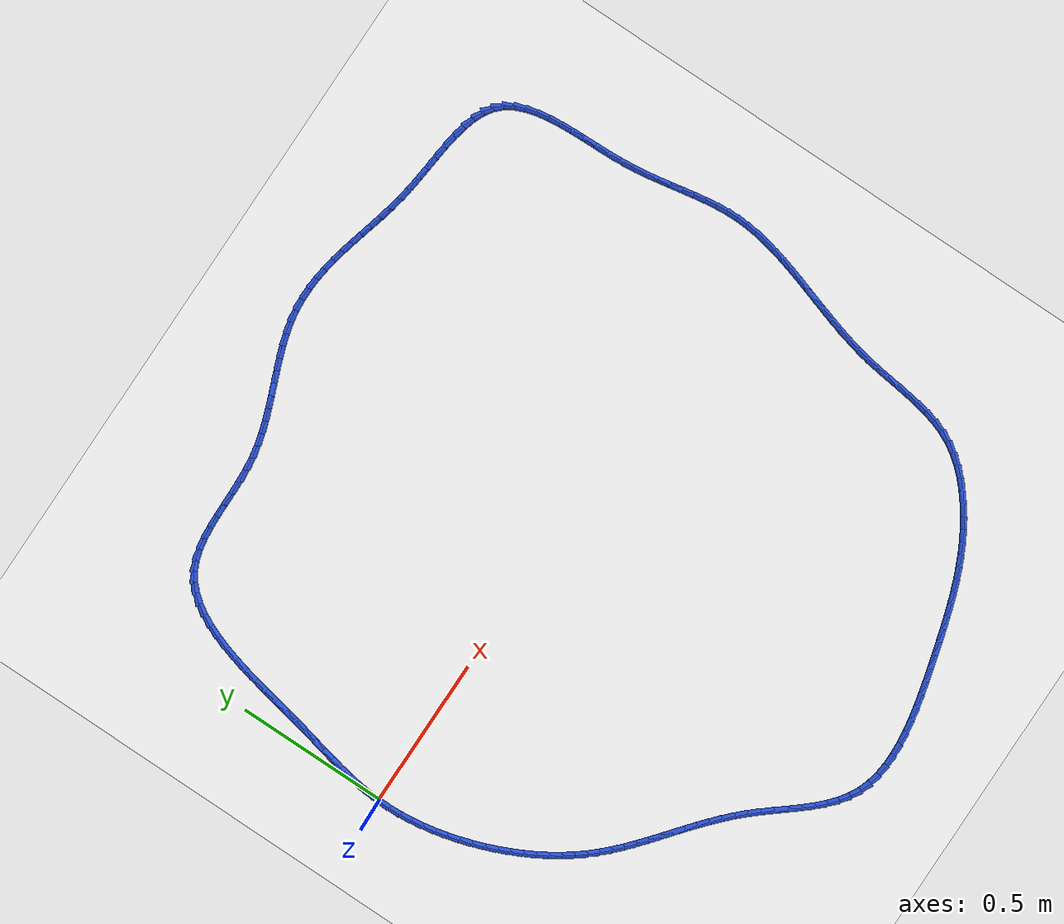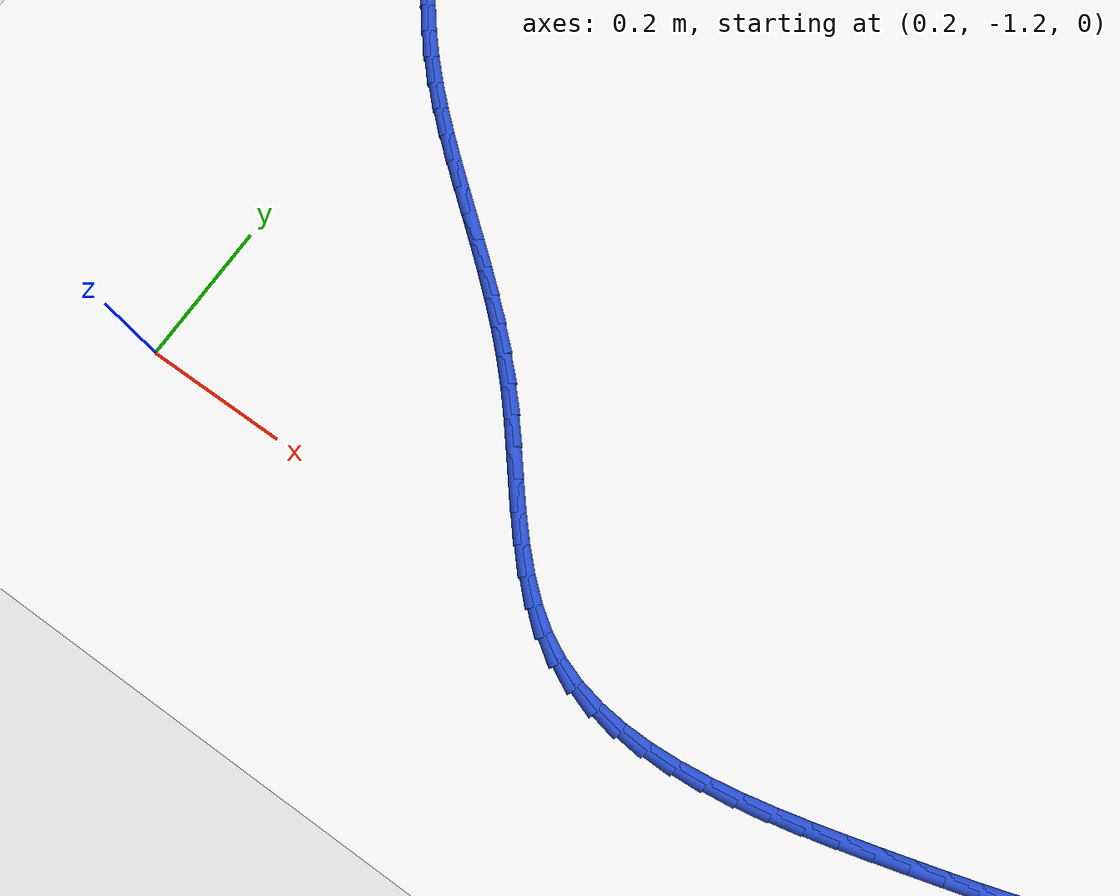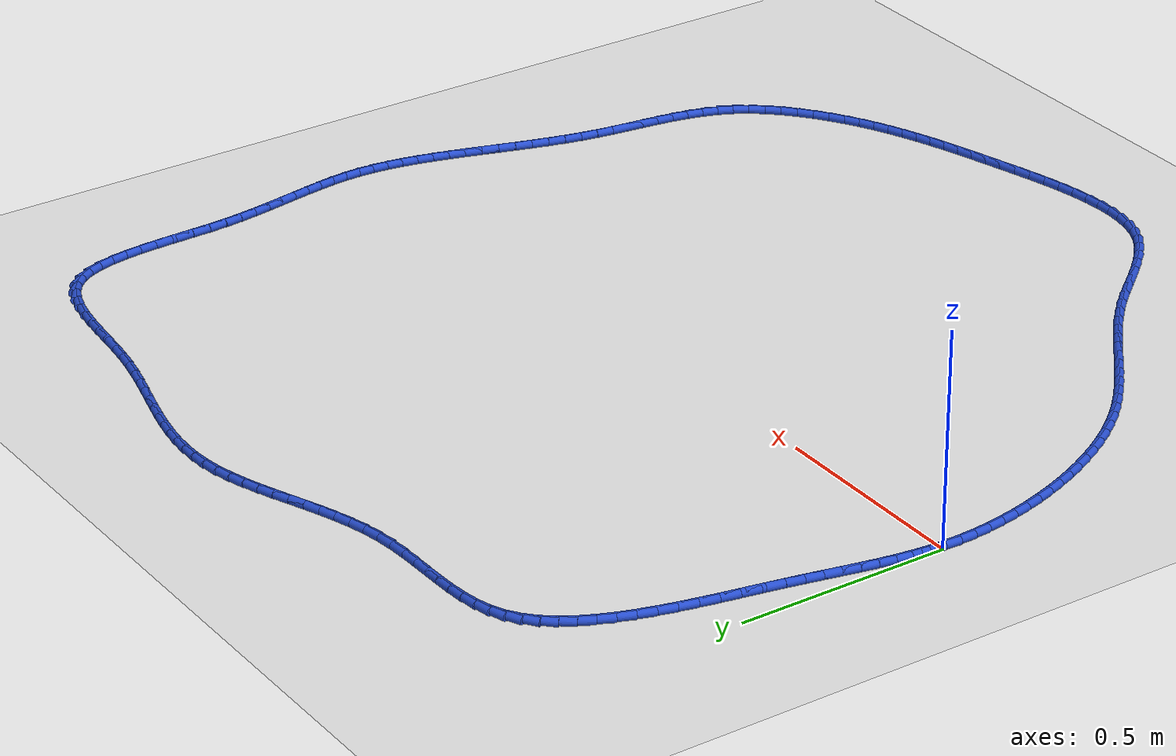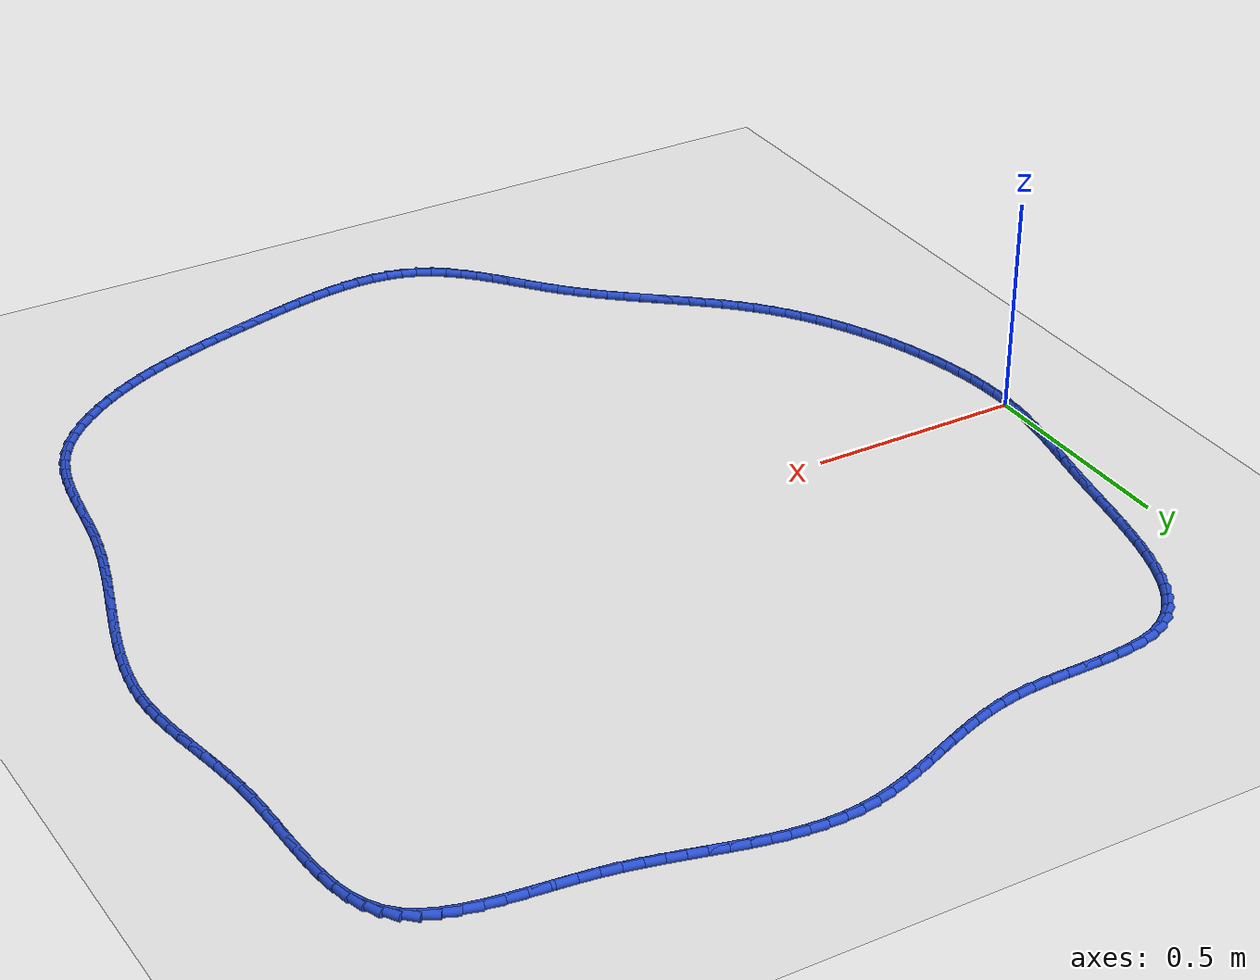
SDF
<sdf version="1.6">
 <world name="default">
  <light name="sun" type="directional">
   <pose>0 0 10 0 -0 0</pose>
   <diffuse>0.8 0.8 0.8 1</diffuse>
   <specular>0.2 0.2 0.2 1</specular>
   <attenuation>
    <range>1000</range>
    <constant>0.9</constant>
    <linear>0.01</linear>
    <quadratic>0.001</quadratic>
   </attenuation>
   <direction>-0.5 0.1 -0.9</direction>
  </light>
  <model name="ground_plane">
   <static>1</static>
   <link name="link">
    <collision name="collision">
     <geometry><plane><normal>0 0 1</normal><size>100 100</size></plane></geometry>
     <surface><friction><ode><mu>100</mu><mu2>50</mu2></ode></friction></surface>
    </collision>
    <visual name="visual">
     <cast_shadows>0</cast_shadows>
     <geometry><plane><normal>0 0 1</normal><size>100 100</size></plane></geometry>
     <material>
      <script><uri>file://media/materials/scripts/gazebo.material</uri><name>Gazebo/WhiteGlow</name></script>
     </material>
    </visual>
   </link>
  </model>
  <gravity>0 0 -9.8</gravity>
  <magnetic_field>6e-06 2.3e-05 -4.2e-05</magnetic_field>
  <atmosphere type="adiabatic"/>
  <physics name="default_physics" default="0" type="ode">
   <max_step_size>0.001</max_step_size>
   <real_time_factor>1</real_time_factor>
   <real_time_update_rate>1000</real_time_update_rate>
  </physics>
  <scene><ambient>0.4 0.4 0.4 1</ambient><background>0.7 0.7 0.7 1</background><shadows>1</shadows></scene>
  <spherical_coordinates>
   <surface_model>EARTH_WGS84</surface_model>
   <latitude_deg>0</latitude_deg>
   <longitude_deg>0</longitude_deg>
   <elevation>0</elevation>
   <heading_deg>0</heading_deg>
  </spherical_coordinates>
  <model name="line">
   <link name="link_0">
    <pose>1.0408340855860843e-17 6.938893903907228e-18 0.01 0 1.57 1.5118387415920338</pose>
    <collision name="collision">
     <geometry><cylinder><radius>0.01</radius><length>0.08</length></cylinder></geometry>
    </collision>
    <visual name="visual">
     <material>
      <script><name>Gazebo/Blue</name><uri>file://media/materials/scripts/gazebo.material</uri></script>
     </material>
     <geometry><cylinder><radius>0.01</radius><length>0.08</length></cylinder></geometry>
    </visual>
   </link>
   <link name="link_1">
    <pose>0.00226688801252979 0.03840491144058814 0.01 0 1.57 1.4633935869433146</pose>
    <collision name="collision">
     <geometry><cylinder><radius>0.01</radius><length>0.08</length></cylinder></geometry>
    </collision>
    <visual name="visual">
     <material>
      <script><name>Gazebo/Blue</name><uri>file://media/materials/scripts/gazebo.material</uri></script>
     </material>
     <geometry><cylinder><radius>0.01</radius><length>0.08</length></cylinder></geometry>
    </visual>
   </link>
   <link name="link_2">
    <pose>0.006378870510455926 0.07654322411985756 0.01 0 1.57 1.4229863500662054</pose>
    <collision name="collision">
     <geometry><cylinder><radius>0.01</radius><length>0.08</length></cylinder></geometry>
    </collision>
    <visual name="visual">
     <material>
      <script><name>Gazebo/Blue</name><uri>file://media/materials/scripts/gazebo.material</uri></script>
     </material>
     <geometry><cylinder><radius>0.01</radius><length>0.08</length></cylinder></geometry>
    </visual>
   </link>
   <link name="link_3">
    <pose>0.012048836085155338 0.1146232871862142 0.01 0 1.57 1.3911986098898457</pose>
    <collision name="collision">
     <geometry><cylinder><radius>0.01</radius><length>0.08</length></cylinder></geometry>
    </collision>
    <visual name="visual">
     <material>
      <script><name>Gazebo/Blue</name><uri>file://media/materials/scripts/gazebo.material</uri></script>
     </material>
     <geometry><cylinder><radius>0.01</radius><length>0.08</length></cylinder></geometry>
    </visual>
   </link>
   <link name="link_4">
    <pose>0.01898967332800496 0.152853449788064 0.01 0 1.57 1.3682512714293409</pose>
    <collision name="collision">
     <geometry><cylinder><radius>0.01</radius><length>0.08</length></cylinder></geometry>
    </collision>
    <visual name="visual">
     <material>
      <script><name>Gazebo/Blue</name><uri>file://media/materials/scripts/gazebo.material</uri></script>
     </material>
     <geometry><cylinder><radius>0.01</radius><length>0.08</length></cylinder></geometry>
    </visual>
   </link>
   <link name="link_5">
    <pose>0.02691427083038169 0.19144206107381276 0.01 0 1.57 1.3540741341417506</pose>
    <collision name="collision">
     <geometry><cylinder><radius>0.01</radius><length>0.08</length></cylinder></geometry>
    </collision>
    <visual name="visual">
     <material>
      <script><name>Gazebo/Blue</name><uri>file://media/materials/scripts/gazebo.material</uri></script>
     </material>
     <geometry><cylinder><radius>0.01</radius><length>0.08</length></cylinder></geometry>
    </visual>
   </link>
   <link name="link_6">
    <pose>0.03553551718366247 0.23059747019186638 0.01 0 1.57 1.3483759285620933</pose>
    <collision name="collision">
     <geometry><cylinder><radius>0.01</radius><length>0.08</length></cylinder></geometry>
    </collision>
    <visual name="visual">
     <material>
      <script><name>Gazebo/Blue</name><uri>file://media/materials/scripts/gazebo.material</uri></script>
     </material>
     <geometry><cylinder><radius>0.01</radius><length>0.08</length></cylinder></geometry>
    </visual>
   </link>
   <link name="link_7">
    <pose>0.04456630097922422 0.2705280262906308 0.01 0 1.57 1.3507024474958809</pose>
    <collision name="collision">
     <geometry><cylinder><radius>0.01</radius><length>0.08</length></cylinder></geometry>
    </collision>
    <visual name="visual">
     <material>
      <script><name>Gazebo/Blue</name><uri>file://media/materials/scripts/gazebo.material</uri></script>
     </material>
     <geometry><cylinder><radius>0.01</radius><length>0.08</length></cylinder></geometry>
    </visual>
   </link>
   <link name="link_8">
    <pose>0.053719510808443824 0.3114420785185118 0.01 0 1.57 1.3604277967275744</pose>
    <collision name="collision">
     <geometry><cylinder><radius>0.01</radius><length>0.08</length></cylinder></geometry>
    </collision>
    <visual name="visual">
     <material>
      <script><name>Gazebo/Blue</name><uri>file://media/materials/scripts/gazebo.material</uri></script>
     </material>
     <geometry><cylinder><radius>0.01</radius><length>0.08</length></cylinder></geometry>
    </visual>
   </link>
   <link name="link_9">
    <pose>0.06270983250188547 0.353545841716148 0.01 0 1.57 1.37199462553629</pose>
    <collision name="collision">
     <geometry><cylinder><radius>0.01</radius><length>0.08</length></cylinder></geometry>
    </collision>
    <visual name="visual">
     <material>
      <script><name>Gazebo/Blue</name><uri>file://media/materials/scripts/gazebo.material</uri></script>
     </material>
     <geometry><cylinder><radius>0.01</radius><length>0.08</length></cylinder></geometry>
    </visual>
   </link>
   <link name="link_10">
    <pose>0.07143064893689718 0.39683331940712946 0.01 0 1.57 1.376511682294516</pose>
    <collision name="collision">
     <geometry><cylinder><radius>0.01</radius><length>0.08</length></cylinder></geometry>
    </collision>
    <visual name="visual">
     <material>
      <script><name>Gazebo/Blue</name><uri>file://media/materials/scripts/gazebo.material</uri></script>
     </material>
     <geometry><cylinder><radius>0.01</radius><length>0.08</length></cylinder></geometry>
    </visual>
   </link>
   <link name="link_11">
    <pose>0.08010328609658643 0.44090906694204857 0.01 0 1.57 1.3734969270097608</pose>
    <collision name="collision">
     <geometry><cylinder><radius>0.01</radius><length>0.08</length></cylinder></geometry>
    </collision>
    <visual name="visual">
     <material>
      <script><name>Gazebo/Blue</name><uri>file://media/materials/scripts/gazebo.material</uri></script>
     </material>
     <geometry><cylinder><radius>0.01</radius><length>0.08</length></cylinder></geometry>
    </visual>
   </link>
   <link name="link_12">
    <pose>0.08898421134203051 0.485335907599054 0.01 0 1.57 1.3630672160436106</pose>
    <collision name="collision">
     <geometry><cylinder><radius>0.01</radius><length>0.08</length></cylinder></geometry>
    </collision>
    <visual name="visual">
     <material>
      <script><name>Gazebo/Blue</name><uri>file://media/materials/scripts/gazebo.material</uri></script>
     </material>
     <geometry><cylinder><radius>0.01</radius><length>0.08</length></cylinder></geometry>
    </visual>
   </link>
   <link name="link_13">
    <pose>0.09832989203430673 0.5296766646562946 0.01 0 1.57 1.3449689978395563</pose>
    <collision name="collision">
     <geometry><cylinder><radius>0.01</radius><length>0.08</length></cylinder></geometry>
    </collision>
    <visual name="visual">
     <material>
      <script><name>Gazebo/Blue</name><uri>file://media/materials/scripts/gazebo.material</uri></script>
     </material>
     <geometry><cylinder><radius>0.01</radius><length>0.08</length></cylinder></geometry>
    </visual>
   </link>
   <link name="link_14">
    <pose>0.10839679553449232 0.573494161391919 0.01 0 1.57 1.3185766301756079</pose>
    <collision name="collision">
     <geometry><cylinder><radius>0.01</radius><length>0.08</length></cylinder></geometry>
    </collision>
    <visual name="visual">
     <material>
      <script><name>Gazebo/Blue</name><uri>file://media/materials/scripts/gazebo.material</uri></script>
     </material>
     <geometry><cylinder><radius>0.01</radius><length>0.08</length></cylinder></geometry>
    </visual>
   </link>
   <link name="link_15">
    <pose>0.11944138920366458 0.6163512210840759 0.01 0 1.57 1.282863482189582</pose>
    <collision name="collision">
     <geometry><cylinder><radius>0.01</radius><length>0.08</length></cylinder></geometry>
    </collision>
    <visual name="visual">
     <material>
      <script><name>Gazebo/Blue</name><uri>file://media/materials/scripts/gazebo.material</uri></script>
     </material>
     <geometry><cylinder><radius>0.01</radius><length>0.08</length></cylinder></geometry>
    </visual>
   </link>
   <link name="link_16">
    <pose>0.1317201404029008 0.6578106670109142 0.01 0 1.57 1.2363547287437564</pose>
    <collision name="collision">
     <geometry><cylinder><radius>0.01</radius><length>0.08</length></cylinder></geometry>
    </collision>
    <visual name="visual">
     <material>
      <script><name>Gazebo/Blue</name><uri>file://media/materials/scripts/gazebo.material</uri></script>
     </material>
     <geometry><cylinder><radius>0.01</radius><length>0.08</length></cylinder></geometry>
    </visual>
   </link>
   <link name="link_17">
    <pose>0.14548951649327824 0.6974353224505824 0.01 0 1.57 1.177081291371161</pose>
    <collision name="collision">
     <geometry><cylinder><radius>0.01</radius><length>0.08</length></cylinder></geometry>
    </collision>
    <visual name="visual">
     <material>
      <script><name>Gazebo/Blue</name><uri>file://media/materials/scripts/gazebo.material</uri></script>
     </material>
     <geometry><cylinder><radius>0.01</radius><length>0.08</length></cylinder></geometry>
    </visual>
   </link>
   <link name="link_18">
    <pose>0.16100598483587425 0.734788010681229 0.01 0 1.57 1.1025810179308921</pose>
    <collision name="collision">
     <geometry><cylinder><radius>0.01</radius><length>0.08</length></cylinder></geometry>
    </collision>
    <visual name="visual">
     <material>
      <script><name>Gazebo/Blue</name><uri>file://media/materials/scripts/gazebo.material</uri></script>
     </material>
     <geometry><cylinder><radius>0.01</radius><length>0.08</length></cylinder></geometry>
    </visual>
   </link>
   <link name="link_19">
    <pose>0.178526012791766 0.7694315549810032 0.01 0 1.57 1.0100472046592999</pose>
    <collision name="collision">
     <geometry><cylinder><radius>0.01</radius><length>0.08</length></cylinder></geometry>
    </collision>
    <visual name="visual">
     <material>
      <script><name>Gazebo/Blue</name><uri>file://media/materials/scripts/gazebo.material</uri></script>
     </material>
     <geometry><cylinder><radius>0.01</radius><length>0.08</length></cylinder></geometry>
    </visual>
   </link>
   <link name="link_20">
    <pose>0.19830606772203088 0.8009287786280536 0.01 0 1.57 0.8968079751505506</pose>
    <collision name="collision">
     <geometry><cylinder><radius>0.01</radius><length>0.08</length></cylinder></geometry>
    </collision>
    <visual name="visual">
     <material>
      <script><name>Gazebo/Blue</name><uri>file://media/materials/scripts/gazebo.material</uri></script>
     </material>
     <geometry><cylinder><radius>0.01</radius><length>0.08</length></cylinder></geometry>
    </visual>
   </link>
   <link name="link_21">
    <pose>0.22060261698774591 0.8288425049005284 0.01 0 1.57 0.7613750651972374</pose>
    <collision name="collision">
     <geometry><cylinder><radius>0.01</radius><length>0.08</length></cylinder></geometry>
    </collision>
    <visual name="visual">
     <material>
      <script><name>Gazebo/Blue</name><uri>file://media/materials/scripts/gazebo.material</uri></script>
     </material>
     <geometry><cylinder><radius>0.01</radius><length>0.08</length></cylinder></geometry>
    </visual>
   </link>
   <link name="link_22">
    <pose>0.24567212794998883 0.8527355570765769 0.01 0 1.57 0.6051136358261643</pose>
    <collision name="collision">
     <geometry><cylinder><radius>0.01</radius><length>0.08</length></cylinder></geometry>
    </collision>
    <visual name="visual">
     <material>
      <script><name>Gazebo/Blue</name><uri>file://media/materials/scripts/gazebo.material</uri></script>
     </material>
     <geometry><cylinder><radius>0.01</radius><length>0.08</length></cylinder></geometry>
    </visual>
   </link>
   <link name="link_23">
    <pose>0.2737710679698366 0.8721707584343474 0.01 0 1.57 0.4364322153317377</pose>
    <collision name="collision">
     <geometry><cylinder><radius>0.01</radius><length>0.08</length></cylinder></geometry>
    </collision>
    <visual name="visual">
     <material>
      <script><name>Gazebo/Blue</name><uri>file://media/materials/scripts/gazebo.material</uri></script>
     </material>
     <geometry><cylinder><radius>0.01</radius><length>0.08</length></cylinder></geometry>
    </visual>
   </link>
   <link name="link_24">
    <pose>0.30511135450970317 0.8867887860084936 0.01 0 1.57 0.28859946413243415</pose>
    <collision name="collision">
     <geometry><cylinder><radius>0.01</radius><length>0.08</length></cylinder></geometry>
    </collision>
    <visual name="visual">
     <material>
      <script><name>Gazebo/Blue</name><uri>file://media/materials/scripts/gazebo.material</uri></script>
     </material>
     <geometry><cylinder><radius>0.01</radius><length>0.08</length></cylinder></geometry>
    </visual>
   </link>
   <link name="link_25">
    <pose>0.3394704301597668 0.8969895890638053 0.01 0 1.57 0.17725807708848731</pose>
    <collision name="collision">
     <geometry><cylinder><radius>0.01</radius><length>0.08</length></cylinder></geometry>
    </collision>
    <visual name="visual">
     <material>
      <script><name>Gazebo/Blue</name><uri>file://media/materials/scripts/gazebo.material</uri></script>
     </material>
     <geometry><cylinder><radius>0.01</radius><length>0.08</length></cylinder></geometry>
    </visual>
   </link>
   <link name="link_26">
    <pose>0.37638054756794925 0.9036016017468476 0.01 0 1.57 0.09858731887423465</pose>
    <collision name="collision">
     <geometry><cylinder><radius>0.01</radius><length>0.08</length></cylinder></geometry>
    </collision>
    <visual name="visual">
     <material>
      <script><name>Gazebo/Blue</name><uri>file://media/materials/scripts/gazebo.material</uri></script>
     </material>
     <geometry><cylinder><radius>0.01</radius><length>0.08</length></cylinder></geometry>
    </visual>
   </link>
   <link name="link_27">
    <pose>0.41537119585321614 0.9074580876452575 0.01 0 1.57 0.04760417692412098</pose>
    <collision name="collision">
     <geometry><cylinder><radius>0.01</radius><length>0.08</length></cylinder></geometry>
    </collision>
    <visual name="visual">
     <material>
      <script><name>Gazebo/Blue</name><uri>file://media/materials/scripts/gazebo.material</uri></script>
     </material>
     <geometry><cylinder><radius>0.01</radius><length>0.08</length></cylinder></geometry>
    </visual>
   </link>
   <link name="link_28">
    <pose>0.45597186413453394 0.9093923103466738 0.01 0 1.57 0.02024686156113432</pose>
    <collision name="collision">
     <geometry><cylinder><radius>0.01</radius><length>0.08</length></cylinder></geometry>
    </collision>
    <visual name="visual">
     <material>
      <script><name>Gazebo/Blue</name><uri>file://media/materials/scripts/gazebo.material</uri></script>
     </material>
     <geometry><cylinder><radius>0.01</radius><length>0.08</length></cylinder></geometry>
    </visual>
   </link>
   <link name="link_29">
    <pose>0.49771204153086834 0.910237533438734 0.01 0 1.57 0.013899093795391119</pose>
    <collision name="collision">
     <geometry><cylinder><radius>0.01</radius><length>0.08</length></cylinder></geometry>
    </collision>
    <visual name="visual">
     <material>
      <script><name>Gazebo/Blue</name><uri>file://media/materials/scripts/gazebo.material</uri></script>
     </material>
     <geometry><cylinder><radius>0.01</radius><length>0.08</length></cylinder></geometry>
    </visual>
   </link>
   <link name="link_30">
    <pose>0.5401212171611854 0.9108270205090762 0.01 0 1.57 0.027382936643818134</pose>
    <collision name="collision">
     <geometry><cylinder><radius>0.01</radius><length>0.08</length></cylinder></geometry>
    </collision>
    <visual name="visual">
     <material>
      <script><name>Gazebo/Blue</name><uri>file://media/materials/scripts/gazebo.material</uri></script>
     </material>
     <geometry><cylinder><radius>0.01</radius><length>0.08</length></cylinder></geometry>
    </visual>
   </link>
   <link name="link_31">
    <pose>0.5827288801444511 0.9119940351453385 0.01 0 1.57 0.06081464934989108</pose>
    <collision name="collision">
     <geometry><cylinder><radius>0.01</radius><length>0.08</length></cylinder></geometry>
    </collision>
    <visual name="visual">
     <material>
      <script><name>Gazebo/Blue</name><uri>file://media/materials/scripts/gazebo.material</uri></script>
     </material>
     <geometry><cylinder><radius>0.01</radius><length>0.08</length></cylinder></geometry>
    </visual>
   </link>
   <link name="link_32">
    <pose>0.6250645195996315 0.9145718409351585 0.01 0 1.57 0.1154125492884915</pose>
    <collision name="collision">
     <geometry><cylinder><radius>0.01</radius><length>0.08</length></cylinder></geometry>
    </collision>
    <visual name="visual">
     <material>
      <script><name>Gazebo/Blue</name><uri>file://media/materials/scripts/gazebo.material</uri></script>
     </material>
     <geometry><cylinder><radius>0.01</radius><length>0.08</length></cylinder></geometry>
    </visual>
   </link>
   <link name="link_33">
    <pose>0.6666576544004259 0.9193936385630586 0.01 0 1.57 0.1861184933495123</pose>
    <collision name="collision">
     <geometry><cylinder><radius>0.01</radius><length>0.08</length></cylinder></geometry>
    </collision>
    <visual name="visual">
     <material>
      <script><name>Gazebo/Blue</name><uri>file://media/materials/scripts/gazebo.material</uri></script>
     </material>
     <geometry><cylinder><radius>0.01</radius><length>0.08</length></cylinder></geometry>
    </visual>
   </link>
   <link name="link_34">
    <pose>0.7071661500160438 0.9270212970697462 0.01 0 1.57 0.25037352740552854</pose>
    <collision name="collision">
     <geometry><cylinder><radius>0.01</radius><length>0.08</length></cylinder></geometry>
    </collision>
    <visual name="visual">
     <material>
      <script><name>Gazebo/Blue</name><uri>file://media/materials/scripts/gazebo.material</uri></script>
     </material>
     <geometry><cylinder><radius>0.01</radius><length>0.08</length></cylinder></geometry>
    </visual>
   </link>
   <link name="link_35">
    <pose>0.7466701175366293 0.9371240354184832 0.01 0 1.57 0.3024261193298521</pose>
    <collision name="collision">
     <geometry><cylinder><radius>0.01</radius><length>0.08</length></cylinder></geometry>
    </collision>
    <visual name="visual">
     <material>
      <script><name>Gazebo/Blue</name><uri>file://media/materials/scripts/gazebo.material</uri></script>
     </material>
     <geometry><cylinder><radius>0.01</radius><length>0.08</length></cylinder></geometry>
    </visual>
   </link>
   <link name="link_36">
    <pose>0.7853363733828381 0.9491877728148566 0.01 0 1.57 0.3416433908659524</pose>
    <collision name="collision">
     <geometry><cylinder><radius>0.01</radius><length>0.08</length></cylinder></geometry>
    </collision>
    <visual name="visual">
     <material>
      <script><name>Gazebo/Blue</name><uri>file://media/materials/scripts/gazebo.material</uri></script>
     </material>
     <geometry><cylinder><radius>0.01</radius><length>0.08</length></cylinder></geometry>
    </visual>
   </link>
   <link name="link_37">
    <pose>0.8233317339753262 0.9626984284644536 0.01 0 1.57 0.3677260126980559</pose>
    <collision name="collision">
     <geometry><cylinder><radius>0.01</radius><length>0.08</length></cylinder></geometry>
    </collision>
    <visual name="visual">
     <material>
      <script><name>Gazebo/Blue</name><uri>file://media/materials/scripts/gazebo.material</uri></script>
     </material>
     <geometry><cylinder><radius>0.01</radius><length>0.08</length></cylinder></geometry>
    </visual>
   </link>
   <link name="link_38">
    <pose>0.8608230157347494 0.9771419215728614 0.01 0 1.57 0.38052127386642065</pose>
    <collision name="collision">
     <geometry><cylinder><radius>0.01</radius><length>0.08</length></cylinder></geometry>
    </collision>
    <visual name="visual">
     <material>
      <script><name>Gazebo/Blue</name><uri>file://media/materials/scripts/gazebo.material</uri></script>
     </material>
     <geometry><cylinder><radius>0.01</radius><length>0.08</length></cylinder></geometry>
    </visual>
   </link>
   <link name="link_39">
    <pose>0.8979770350817641 0.9920041713456675 0.01 0 1.57 0.3798884362495175</pose>
    <collision name="collision">
     <geometry><cylinder><radius>0.01</radius><length>0.08</length></cylinder></geometry>
    </collision>
    <visual name="visual">
     <material>
      <script><name>Gazebo/Blue</name><uri>file://media/materials/scripts/gazebo.material</uri></script>
     </material>
     <geometry><cylinder><radius>0.01</radius><length>0.08</length></cylinder></geometry>
    </visual>
   </link>
   <link name="link_40">
    <pose>0.9349606084370259 1.0067710969884591 0.01 0 1.57 0.36562912412861653</pose>
    <collision name="collision">
     <geometry><cylinder><radius>0.01</radius><length>0.08</length></cylinder></geometry>
    </collision>
    <visual name="visual">
     <material>
      <script><name>Gazebo/Blue</name><uri>file://media/materials/scripts/gazebo.material</uri></script>
     </material>
     <geometry><cylinder><radius>0.01</radius><length>0.08</length></cylinder></geometry>
    </visual>
   </link>
   <link name="link_41">
    <pose>0.9719405522211906 1.0209286177068233 0.01 0 1.57 0.33748861234512556</pose>
    <collision name="collision">
     <geometry><cylinder><radius>0.01</radius><length>0.08</length></cylinder></geometry>
    </collision>
    <visual name="visual">
     <material>
      <script><name>Gazebo/Blue</name><uri>file://media/materials/scripts/gazebo.material</uri></script>
     </material>
     <geometry><cylinder><radius>0.01</radius><length>0.08</length></cylinder></geometry>
    </visual>
   </link>
   <link name="link_42">
    <pose>1.0090836828549146 1.0339626527063472 0.01 0 1.57 0.2952357071792602</pose>
    <collision name="collision">
     <geometry><cylinder><radius>0.01</radius><length>0.08</length></cylinder></geometry>
    </collision>
    <visual name="visual">
     <material>
      <script><name>Gazebo/Blue</name><uri>file://media/materials/scripts/gazebo.material</uri></script>
     </material>
     <geometry><cylinder><radius>0.01</radius><length>0.08</length></cylinder></geometry>
    </visual>
   </link>
   <link name="link_43">
    <pose>1.0465568167588537 1.0453591211926185 0.01 0 1.57 0.23883027747730567</pose>
    <collision name="collision">
     <geometry><cylinder><radius>0.01</radius><length>0.08</length></cylinder></geometry>
    </collision>
    <visual name="visual">
     <material>
      <script><name>Gazebo/Blue</name><uri>file://media/materials/scripts/gazebo.material</uri></script>
     </material>
     <geometry><cylinder><radius>0.01</radius><length>0.08</length></cylinder></geometry>
    </visual>
   </link>
   <link name="link_44">
    <pose>1.0845267703536634 1.0546039423712241 0.01 0 1.57 0.1686765028902553</pose>
    <collision name="collision">
     <geometry><cylinder><radius>0.01</radius><length>0.08</length></cylinder></geometry>
    </collision>
    <visual name="visual">
     <material>
      <script><name>Gazebo/Blue</name><uri>file://media/materials/scripts/gazebo.material</uri></script>
     </material>
     <geometry><cylinder><radius>0.01</radius><length>0.08</length></cylinder></geometry>
    </visual>
   </link>
   <link name="link_45">
    <pose>1.12316036006 1.061183035447751 0.01 0 1.57 0.08615382812635393</pose>
    <collision name="collision">
     <geometry><cylinder><radius>0.01</radius><length>0.08</length></cylinder></geometry>
    </collision>
    <visual name="visual">
     <material>
      <script><name>Gazebo/Blue</name><uri>file://media/materials/scripts/gazebo.material</uri></script>
     </material>
     <geometry><cylinder><radius>0.01</radius><length>0.08</length></cylinder></geometry>
    </visual>
   </link>
   <link name="link_46">
    <pose>1.16261064117979 1.0645902623882741 0.01 0 1.57 0.00502083160346573</pose>
    <collision name="collision">
     <geometry><cylinder><radius>0.01</radius><length>0.08</length></cylinder></geometry>
    </collision>
    <visual name="visual">
     <material>
      <script><name>Gazebo/Blue</name><uri>file://media/materials/scripts/gazebo.material</uri></script>
     </material>
     <geometry><cylinder><radius>0.01</radius><length>0.08</length></cylinder></geometry>
    </visual>
   </link>
   <link name="link_47">
    <pose>1.2022423870300716 1.0647892483824053 0.01 0 1.57 -0.06354605870823674</pose>
    <collision name="collision">
     <geometry><cylinder><radius>0.01</radius><length>0.08</length></cylinder></geometry>
    </collision>
    <visual name="visual">
     <material>
      <script><name>Gazebo/Blue</name><uri>file://media/materials/scripts/gazebo.material</uri></script>
     </material>
     <geometry><cylinder><radius>0.01</radius><length>0.08</length></cylinder></geometry>
    </visual>
   </link>
   <link name="link_48">
    <pose>1.2411630865288392 1.062312656853271 0.01 0 1.57 -0.12308139145691359</pose>
    <collision name="collision">
     <geometry><cylinder><radius>0.01</radius><length>0.08</length></cylinder></geometry>
    </collision>
    <visual name="visual">
     <material>
      <script><name>Gazebo/Blue</name><uri>file://media/materials/scripts/gazebo.material</uri></script>
     </material>
     <geometry><cylinder><radius>0.01</radius><length>0.08</length></cylinder></geometry>
    </visual>
   </link>
   <link name="link_49">
    <pose>1.2795118479128234 1.0575686580545207 0.01 0 1.57 -0.17241051413102854</pose>
    <collision name="collision">
     <geometry><cylinder><radius>0.01</radius><length>0.08</length></cylinder></geometry>
    </collision>
    <visual name="visual">
     <material>
      <script><name>Gazebo/Blue</name><uri>file://media/materials/scripts/gazebo.material</uri></script>
     </material>
     <geometry><cylinder><radius>0.01</radius><length>0.08</length></cylinder></geometry>
    </visual>
   </link>
   <link name="link_50">
    <pose>1.317488119043359 1.0509554931102754 0.01 0 1.57 -0.21067340956524688</pose>
    <collision name="collision">
     <geometry><cylinder><radius>0.01</radius><length>0.08</length></cylinder></geometry>
    </collision>
    <visual name="visual">
     <material>
      <script><name>Gazebo/Blue</name><uri>file://media/materials/scripts/gazebo.material</uri></script>
     </material>
     <geometry><cylinder><radius>0.01</radius><length>0.08</length></cylinder></geometry>
    </visual>
   </link>
   <link name="link_51">
    <pose>1.355291347781783 1.0428714031446573 0.01 0 1.57 -0.23748519735594778</pose>
    <collision name="collision">
     <geometry><cylinder><radius>0.01</radius><length>0.08</length></cylinder></geometry>
    </collision>
    <visual name="visual">
     <material>
      <script><name>Gazebo/Blue</name><uri>file://media/materials/scripts/gazebo.material</uri></script>
     </material>
     <geometry><cylinder><radius>0.01</radius><length>0.08</length></cylinder></geometry>
    </visual>
   </link>
   <link name="link_52">
    <pose>1.3931209819894317 1.0337146292817885 0.01 0 1.57 -0.2528116050552469</pose>
    <collision name="collision">
     <geometry><cylinder><radius>0.01</radius><length>0.08</length></cylinder></geometry>
    </collision>
    <visual name="visual">
     <material>
      <script><name>Gazebo/Blue</name><uri>file://media/materials/scripts/gazebo.material</uri></script>
     </material>
     <geometry><cylinder><radius>0.01</radius><length>0.08</length></cylinder></geometry>
    </visual>
   </link>
   <link name="link_53">
    <pose>1.4311764695276405 1.023883412645791 0.01 0 1.57 -0.25685933071088174</pose>
    <collision name="collision">
     <geometry><cylinder><radius>0.01</radius><length>0.08</length></cylinder></geometry>
    </collision>
    <visual name="visual">
     <material>
      <script><name>Gazebo/Blue</name><uri>file://media/materials/scripts/gazebo.material</uri></script>
     </material>
     <geometry><cylinder><radius>0.01</radius><length>0.08</length></cylinder></geometry>
    </visual>
   </link>
   <link name="link_54">
    <pose>1.469657258257746 1.013775994360786 0.01 0 1.57 -0.2500022965165465</pose>
    <collision name="collision">
     <geometry><cylinder><radius>0.01</radius><length>0.08</length></cylinder></geometry>
    </collision>
    <visual name="visual">
     <material>
      <script><name>Gazebo/Blue</name><uri>file://media/materials/scripts/gazebo.material</uri></script>
     </material>
     <geometry><cylinder><radius>0.01</radius><length>0.08</length></cylinder></geometry>
    </visual>
   </link>
   <link name="link_55">
    <pose>1.508762796041085 1.0037906155508962 0.01 0 1.57 -0.23274796626748584</pose>
    <collision name="collision">
     <geometry><cylinder><radius>0.01</radius><length>0.08</length></cylinder></geometry>
    </collision>
    <visual name="visual">
     <material>
      <script><name>Gazebo/Blue</name><uri>file://media/materials/scripts/gazebo.material</uri></script>
     </material>
     <geometry><cylinder><radius>0.01</radius><length>0.08</length></cylinder></geometry>
    </visual>
   </link>
   <link name="link_56">
    <pose>1.548692530738993 0.994325517340243 0.01 0 1.57 -0.20573756306394303</pose>
    <collision name="collision">
     <geometry><cylinder><radius>0.01</radius><length>0.08</length></cylinder></geometry>
    </collision>
    <visual name="visual">
     <material>
      <script><name>Gazebo/Blue</name><uri>file://media/materials/scripts/gazebo.material</uri></script>
     </material>
     <geometry><cylinder><radius>0.01</radius><length>0.08</length></cylinder></geometry>
    </visual>
   </link>
   <link name="link_57">
    <pose>1.589645910212806 0.9857789408529487 0.01 0 1.57 -0.16976822002471317</pose>
    <collision name="collision">
     <geometry><cylinder><radius>0.01</radius><length>0.08</length></cylinder></geometry>
    </collision>
    <visual name="visual">
     <material>
      <script><name>Gazebo/Blue</name><uri>file://media/materials/scripts/gazebo.material</uri></script>
     </material>
     <geometry><cylinder><radius>0.01</radius><length>0.08</length></cylinder></geometry>
    </visual>
   </link>
   <link name="link_58">
    <pose>1.6318223807164862 0.9785491252672874 0.01 0 1.57 -0.13084393198189373</pose>
    <collision name="collision">
     <geometry><cylinder><radius>0.01</radius><length>0.08</length></cylinder></geometry>
    </collision>
    <visual name="visual">
     <material>
      <script><name>Gazebo/Blue</name><uri>file://media/materials/scripts/gazebo.material</uri></script>
     </material>
     <geometry><cylinder><radius>0.01</radius><length>0.08</length></cylinder></geometry>
    </visual>
   </link>
   <link name="link_59">
    <pose>1.6752555157815856 0.972833508432283 0.01 0 1.57 -0.10743513473527333</pose>
    <collision name="collision">
     <geometry><cylinder><radius>0.01</radius><length>0.08</length></cylinder></geometry>
    </collision>
    <visual name="visual">
     <material>
      <script><name>Gazebo/Blue</name><uri>file://media/materials/scripts/gazebo.material</uri></script>
     </material>
     <geometry><cylinder><radius>0.01</radius><length>0.08</length></cylinder></geometry>
    </visual>
   </link>
   <link name="link_60">
    <pose>1.7193573492685708 0.9680771079658004 0.01 0 1.57 -0.10247079330258022</pose>
    <collision name="collision">
     <geometry><cylinder><radius>0.01</radius><length>0.08</length></cylinder></geometry>
    </collision>
    <visual name="visual">
     <material>
      <script><name>Gazebo/Blue</name><uri>file://media/materials/scripts/gazebo.material</uri></script>
     </material>
     <geometry><cylinder><radius>0.01</radius><length>0.08</length></cylinder></geometry>
    </visual>
   </link>
   <link name="link_61">
    <pose>1.7633943626774469 0.9635487394735153 0.01 0 1.57 -0.11584519909751555</pose>
    <collision name="collision">
     <geometry><cylinder><radius>0.01</radius><length>0.08</length></cylinder></geometry>
    </collision>
    <visual name="visual">
     <material>
      <script><name>Gazebo/Blue</name><uri>file://media/materials/scripts/gazebo.material</uri></script>
     </material>
     <geometry><cylinder><radius>0.01</radius><length>0.08</length></cylinder></geometry>
    </visual>
   </link>
   <link name="link_62">
    <pose>1.8066330375082216 0.9585172185611044 0.01 0 1.57 -0.14912056485801523</pose>
    <collision name="collision">
     <geometry><cylinder><radius>0.01</radius><length>0.08</length></cylinder></geometry>
    </collision>
    <visual name="visual">
     <material>
      <script><name>Gazebo/Blue</name><uri>file://media/materials/scripts/gazebo.material</uri></script>
     </material>
     <geometry><cylinder><radius>0.01</radius><length>0.08</length></cylinder></geometry>
    </visual>
   </link>
   <link name="link_63">
    <pose>1.848339855260902 0.9522513608342431 0.01 0 1.57 -0.2057455618452677</pose>
    <collision name="collision">
     <geometry><cylinder><radius>0.01</radius><length>0.08</length></cylinder></geometry>
    </collision>
    <visual name="visual">
     <material>
      <script><name>Gazebo/Blue</name><uri>file://media/materials/scripts/gazebo.material</uri></script>
     </material>
     <geometry><cylinder><radius>0.01</radius><length>0.08</length></cylinder></geometry>
    </visual>
   </link>
   <link name="link_64">
    <pose>1.8877812974354955 0.9440199818986081 0.01 0 1.57 -0.291338975356333</pose>
    <collision name="collision">
     <geometry><cylinder><radius>0.01</radius><length>0.08</length></cylinder></geometry>
    </collision>
    <visual name="visual">
     <material>
      <script><name>Gazebo/Blue</name><uri>file://media/materials/scripts/gazebo.material</uri></script>
     </material>
     <geometry><cylinder><radius>0.01</radius><length>0.08</length></cylinder></geometry>
    </visual>
   </link>
   <link name="link_65">
    <pose>1.9242238455320082 0.9330918973598753 0.01 0 1.57 -0.4135720012492433</pose>
    <collision name="collision">
     <geometry><cylinder><radius>0.01</radius><length>0.08</length></cylinder></geometry>
    </collision>
    <visual name="visual">
     <material>
      <script><name>Gazebo/Blue</name><uri>file://media/materials/scripts/gazebo.material</uri></script>
     </material>
     <geometry><cylinder><radius>0.01</radius><length>0.08</length></cylinder></geometry>
    </visual>
   </link>
   <link name="link_66">
    <pose>1.9569339810504482 0.9187359228237209 0.01 0 1.57 -0.5802560346704803</pose>
    <collision name="collision">
     <geometry><cylinder><radius>0.01</radius><length>0.08</length></cylinder></geometry>
    </collision>
    <visual name="visual">
     <material>
      <script><name>Gazebo/Blue</name><uri>file://media/materials/scripts/gazebo.material</uri></script>
     </material>
     <geometry><cylinder><radius>0.01</radius><length>0.08</length></cylinder></geometry>
    </visual>
   </link>
   <link name="link_67">
    <pose>1.9851781854908206 0.9002208738958205 0.01 0 1.57 -0.7906833655115915</pose>
    <collision name="collision">
     <geometry><cylinder><radius>0.01</radius><length>0.08</length></cylinder></geometry>
    </collision>
    <visual name="visual">
     <material>
      <script><name>Gazebo/Blue</name><uri>file://media/materials/scripts/gazebo.material</uri></script>
     </material>
     <geometry><cylinder><radius>0.01</radius><length>0.08</length></cylinder></geometry>
    </visual>
   </link>
   <link name="link_68">
    <pose>2.008282026737582 0.8768715158157272 0.01 0 1.57 -0.9997749384667465</pose>
    <collision name="collision">
     <geometry><cylinder><radius>0.01</radius><length>0.08</length></cylinder></geometry>
    </collision>
    <visual name="visual">
     <material>
      <script><name>Gazebo/Blue</name><uri>file://media/materials/scripts/gazebo.material</uri></script>
     </material>
     <geometry><cylinder><radius>0.01</radius><length>0.08</length></cylinder></geometry>
    </visual>
   </link>
   <link name="link_69">
    <pose>2.02634842205702 0.8487486956414175 0.01 0 1.57 -1.170355045484224</pose>
    <collision name="collision">
     <geometry><cylinder><radius>0.01</radius><length>0.08</length></cylinder></geometry>
    </collision>
    <visual name="visual">
     <material>
      <script><name>Gazebo/Blue</name><uri>file://media/materials/scripts/gazebo.material</uri></script>
     </material>
     <geometry><cylinder><radius>0.01</radius><length>0.08</length></cylinder></geometry>
    </visual>
   </link>
   <link name="link_70">
    <pose>2.040028399262602 0.8164322731395562 0.01 0 1.57 -1.3004057428306575</pose>
    <collision name="collision">
     <geometry><cylinder><radius>0.01</radius><length>0.08</length></cylinder></geometry>
    </collision>
    <visual name="visual">
     <material>
      <script><name>Gazebo/Blue</name><uri>file://media/materials/scripts/gazebo.material</uri></script>
     </material>
     <geometry><cylinder><radius>0.01</radius><length>0.08</length></cylinder></geometry>
    </visual>
   </link>
   <link name="link_71">
    <pose>2.0499844628483346 0.7805129754886541 0.01 0 1.57 -1.3955163949866203</pose>
    <collision name="collision">
     <geometry><cylinder><radius>0.01</radius><length>0.08</length></cylinder></geometry>
    </collision>
    <visual name="visual">
     <material>
      <script><name>Gazebo/Blue</name><uri>file://media/materials/scripts/gazebo.material</uri></script>
     </material>
     <geometry><cylinder><radius>0.01</radius><length>0.08</length></cylinder></geometry>
    </visual>
   </link>
   <link name="link_72">
    <pose>2.0568791173082235 0.741581529867222 0.01 0 1.57 -1.462504870447982</pose>
    <collision name="collision">
     <geometry><cylinder><radius>0.01</radius><length>0.08</length></cylinder></geometry>
    </collision>
    <visual name="visual">
     <material>
      <script><name>Gazebo/Blue</name><uri>file://media/materials/scripts/gazebo.material</uri></script>
     </material>
     <geometry><cylinder><radius>0.01</radius><length>0.08</length></cylinder></geometry>
    </visual>
   </link>
   <link name="link_73">
    <pose>2.0613748671362737 0.7002286634537707 0.01 0 1.57 -1.5069849270187068</pose>
    <collision name="collision">
     <geometry><cylinder><radius>0.01</radius><length>0.08</length></cylinder></geometry>
    </collision>
    <visual name="visual">
     <material>
      <script><name>Gazebo/Blue</name><uri>file://media/materials/scripts/gazebo.material</uri></script>
     </material>
     <geometry><cylinder><radius>0.01</radius><length>0.08</length></cylinder></geometry>
    </visual>
   </link>
   <link name="link_74">
    <pose>2.0641342168264925 0.6570451034268106 0.01 0 1.57 -1.5328739431264382</pose>
    <collision name="collision">
     <geometry><cylinder><radius>0.01</radius><length>0.08</length></cylinder></geometry>
    </collision>
    <visual name="visual">
     <material>
      <script><name>Gazebo/Blue</name><uri>file://media/materials/scripts/gazebo.material</uri></script>
     </material>
     <geometry><cylinder><radius>0.01</radius><length>0.08</length></cylinder></geometry>
    </visual>
   </link>
   <link name="link_75">
    <pose>2.0658196708728847 0.612621576964853 0.01 0 1.57 -1.5425370507481455</pose>
    <collision name="collision">
     <geometry><cylinder><radius>0.01</radius><length>0.08</length></cylinder></geometry>
    </collision>
    <visual name="visual">
     <material>
      <script><name>Gazebo/Blue</name><uri>file://media/materials/scripts/gazebo.material</uri></script>
     </material>
     <geometry><cylinder><radius>0.01</radius><length>0.08</length></cylinder></geometry>
    </visual>
   </link>
   <link name="link_76">
    <pose>2.0670937337694575 0.5675488112464088 0.01 0 1.57 -1.5370149648665443</pose>
    <collision name="collision">
     <geometry><cylinder><radius>0.01</radius><length>0.08</length></cylinder></geometry>
    </collision>
    <visual name="visual">
     <material>
      <script><name>Gazebo/Blue</name><uri>file://media/materials/scripts/gazebo.material</uri></script>
     </material>
     <geometry><cylinder><radius>0.01</radius><length>0.08</length></cylinder></geometry>
    </visual>
   </link>
   <link name="link_77">
    <pose>2.068618910010215 0.5224175334499878 0.01 0 1.57 -1.516168102248437</pose>
    <collision name="collision">
     <geometry><cylinder><radius>0.01</radius><length>0.08</length></cylinder></geometry>
    </collision>
    <visual name="visual">
     <material>
      <script><name>Gazebo/Blue</name><uri>file://media/materials/scripts/gazebo.material</uri></script>
     </material>
     <geometry><cylinder><radius>0.01</radius><length>0.08</length></cylinder></geometry>
    </visual>
   </link>
   <link name="link_78">
    <pose>2.0710577040891653 0.47781847075410205 0.01 0 1.57 -1.479744158521406</pose>
    <collision name="collision">
     <geometry><cylinder><radius>0.01</radius><length>0.08</length></cylinder></geometry>
    </collision>
    <visual name="visual">
     <material>
      <script><name>Gazebo/Blue</name><uri>file://media/materials/scripts/gazebo.material</uri></script>
     </material>
     <geometry><cylinder><radius>0.01</radius><length>0.08</length></cylinder></geometry>
    </visual>
   </link>
   <link name="link_79">
    <pose>2.07502982569719 0.4343144152568177 0.01 0 1.57 -1.4411196240991653</pose>
    <collision name="collision">
     <geometry><cylinder><radius>0.01</radius><length>0.08</length></cylinder></geometry>
    </collision>
    <visual name="visual">
     <material>
      <script><name>Gazebo/Blue</name><uri>file://media/materials/scripts/gazebo.material</uri></script>
     </material>
     <geometry><cylinder><radius>0.01</radius><length>0.08</length></cylinder></geometry>
    </visual>
   </link>
   <link name="link_80">
    <pose>2.080539341135744 0.39206628671765337 0.01 0 1.57 -1.4119477316533582</pose>
    <collision name="collision">
     <geometry><cylinder><radius>0.01</radius><length>0.08</length></cylinder></geometry>
    </collision>
    <visual name="visual">
     <material>
      <script><name>Gazebo/Blue</name><uri>file://media/materials/scripts/gazebo.material</uri></script>
     </material>
     <geometry><cylinder><radius>0.01</radius><length>0.08</length></cylinder></geometry>
    </visual>
   </link>
   <link name="link_81">
    <pose>2.087128713516291 0.35093368507912615 0.01 0 1.57 -1.3934064803781783</pose>
    <collision name="collision">
     <geometry><cylinder><radius>0.01</radius><length>0.08</length></cylinder></geometry>
    </collision>
    <visual name="visual">
     <material>
      <script><name>Gazebo/Blue</name><uri>file://media/materials/scripts/gazebo.material</uri></script>
     </material>
     <geometry><cylinder><radius>0.01</radius><length>0.08</length></cylinder></geometry>
    </visual>
   </link>
   <link name="link_82">
    <pose>2.0943292222444954 0.31076890991785544 0.01 0 1.57 -1.3862881607513446</pose>
    <collision name="collision">
     <geometry><cylinder><radius>0.01</radius><length>0.08</length></cylinder></geometry>
    </collision>
    <visual name="visual">
     <material>
      <script><name>Gazebo/Blue</name><uri>file://media/materials/scripts/gazebo.material</uri></script>
     </material>
     <geometry><cylinder><radius>0.01</radius><length>0.08</length></cylinder></geometry>
    </visual>
   </link>
   <link name="link_83">
    <pose>2.101672146726018 0.27142426081046084 0.01 0 1.57 -1.391310648379787</pose>
    <collision name="collision">
     <geometry><cylinder><radius>0.01</radius><length>0.08</length></cylinder></geometry>
    </collision>
    <visual name="visual">
     <material>
      <script><name>Gazebo/Blue</name><uri>file://media/materials/scripts/gazebo.material</uri></script>
     </material>
     <geometry><cylinder><radius>0.01</radius><length>0.08</length></cylinder></geometry>
    </visual>
   </link>
   <link name="link_84">
    <pose>2.1086887663665226 0.23275203733356306 0.01 0 1.57 -1.4091266235786877</pose>
    <collision name="collision">
     <geometry><cylinder><radius>0.01</radius><length>0.08</length></cylinder></geometry>
    </collision>
    <visual name="visual">
     <material>
      <script><name>Gazebo/Blue</name><uri>file://media/materials/scripts/gazebo.material</uri></script>
     </material>
     <geometry><cylinder><radius>0.01</radius><length>0.08</length></cylinder></geometry>
    </visual>
   </link>
   <link name="link_85">
    <pose>2.1149103605716713 0.19460453906378122 0.01 0 1.57 -1.4402799689647814</pose>
    <collision name="collision">
     <geometry><cylinder><radius>0.01</radius><length>0.08</length></cylinder></geometry>
    </collision>
    <visual name="visual">
     <material>
      <script><name>Gazebo/Blue</name><uri>file://media/materials/scripts/gazebo.material</uri></script>
     </material>
     <geometry><cylinder><radius>0.01</radius><length>0.08</length></cylinder></geometry>
    </visual>
   </link>
   <link name="link_86">
    <pose>2.119868208747126 0.15683406557773585 0.01 0 1.57 -1.4850908943707237</pose>
    <collision name="collision">
     <geometry><cylinder><radius>0.01</radius><length>0.08</length></cylinder></geometry>
    </collision>
    <visual name="visual">
     <material>
      <script><name>Gazebo/Blue</name><uri>file://media/materials/scripts/gazebo.material</uri></script>
     </material>
     <geometry><cylinder><radius>0.01</radius><length>0.08</length></cylinder></geometry>
    </visual>
   </link>
   <link name="link_87">
    <pose>2.1230935902985504 0.11929291645204661 0.01 0 1.57 -1.543461777566761</pose>
    <collision name="collision">
     <geometry><cylinder><radius>0.01</radius><length>0.08</length></cylinder></geometry>
    </collision>
    <visual name="visual">
     <material>
      <script><name>Gazebo/Blue</name><uri>file://media/materials/scripts/gazebo.material</uri></script>
     </material>
     <geometry><cylinder><radius>0.01</radius><length>0.08</length></cylinder></geometry>
    </visual>
   </link>
   <link name="link_88">
    <pose>2.124117784631606 0.08183339126333301 0.01 0 1.57 1.5301817495891665</pose>
    <collision name="collision">
     <geometry><cylinder><radius>0.01</radius><length>0.08</length></cylinder></geometry>
    </collision>
    <visual name="visual">
     <material>
      <script><name>Gazebo/Blue</name><uri>file://media/materials/scripts/gazebo.material</uri></script>
     </material>
     <geometry><cylinder><radius>0.01</radius><length>0.08</length></cylinder></geometry>
    </visual>
   </link>
   <link name="link_89">
    <pose>2.122593690683846 0.044328240639109305 0.01 0 1.57 1.467159769155734</pose>
    <collision name="collision">
     <geometry><cylinder><radius>0.01</radius><length>0.08</length></cylinder></geometry>
    </collision>
    <visual name="visual">
     <material>
      <script><name>Gazebo/Blue</name><uri>file://media/materials/scripts/gazebo.material</uri></script>
     </material>
     <geometry><cylinder><radius>0.01</radius><length>0.08</length></cylinder></geometry>
    </visual>
   </link>
   <link name="link_90">
    <pose>2.1186837411773807 0.006735896356931243 0.01 0 1.57 1.4129645011971836</pose>
    <collision name="collision">
     <geometry><cylinder><radius>0.01</radius><length>0.08</length></cylinder></geometry>
    </collision>
    <visual name="visual">
     <material>
      <script><name>Gazebo/Blue</name><uri>file://media/materials/scripts/gazebo.material</uri></script>
     </material>
     <geometry><cylinder><radius>0.01</radius><length>0.08</length></cylinder></geometry>
    </visual>
   </link>
   <link name="link_91">
    <pose>2.11268378676026 -0.03096277478430328 0.01 0 1.57 1.3675789740026905</pose>
    <collision name="collision">
     <geometry><cylinder><radius>0.01</radius><length>0.08</length></cylinder></geometry>
    </collision>
    <visual name="visual">
     <material>
      <script><name>Gazebo/Blue</name><uri>file://media/materials/scripts/gazebo.material</uri></script>
     </material>
     <geometry><cylinder><radius>0.01</radius><length>0.08</length></cylinder></geometry>
    </visual>
   </link>
   <link name="link_92">
    <pose>2.1048896785489 -0.06878690590693878 0.01 0 1.57 1.3307757046805635</pose>
    <collision name="collision">
     <geometry><cylinder><radius>0.01</radius><length>0.08</length></cylinder></geometry>
    </collision>
    <visual name="visual">
     <material>
      <script><name>Gazebo/Blue</name><uri>file://media/materials/scripts/gazebo.material</uri></script>
     </material>
     <geometry><cylinder><radius>0.01</radius><length>0.08</length></cylinder></geometry>
    </visual>
   </link>
   <link name="link_93">
    <pose>2.0955972676597177 -0.10675563013331746 0.01 0 1.57 1.3022243899774284</pose>
    <collision name="collision">
     <geometry><cylinder><radius>0.01</radius><length>0.08</length></cylinder></geometry>
    </collision>
    <visual name="visual">
     <material>
      <script><name>Gazebo/Blue</name><uri>file://media/materials/scripts/gazebo.material</uri></script>
     </material>
     <geometry><cylinder><radius>0.01</radius><length>0.08</length></cylinder></geometry>
    </visual>
   </link>
   <link name="link_94">
    <pose>2.0851024052091263 -0.14488808058578379 0.01 0 1.57 1.2815709500604193</pose>
    <collision name="collision">
     <geometry><cylinder><radius>0.01</radius><length>0.08</length></cylinder></geometry>
    </collision>
    <visual name="visual">
     <material>
      <script><name>Gazebo/Blue</name><uri>file://media/materials/scripts/gazebo.material</uri></script>
     </material>
     <geometry><cylinder><radius>0.01</radius><length>0.08</length></cylinder></geometry>
    </visual>
   </link>
   <link name="link_95">
    <pose>2.0737009423135437 -0.1832033903866816 0.01 0 1.57 1.2684897429278303</pose>
    <collision name="collision">
     <geometry><cylinder><radius>0.01</radius><length>0.08</length></cylinder></geometry>
    </collision>
    <visual name="visual">
     <material>
      <script><name>Gazebo/Blue</name><uri>file://media/materials/scripts/gazebo.material</uri></script>
     </material>
     <geometry><cylinder><radius>0.01</radius><length>0.08</length></cylinder></geometry>
    </visual>
   </link>
   <link name="link_96">
    <pose>2.0616887300893842 -0.2217206926583545 0.01 0 1.57 1.2627143145330293</pose>
    <collision name="collision">
     <geometry><cylinder><radius>0.01</radius><length>0.08</length></cylinder></geometry>
    </collision>
    <visual name="visual">
     <material>
      <script><name>Gazebo/Blue</name><uri>file://media/materials/scripts/gazebo.material</uri></script>
     </material>
     <geometry><cylinder><radius>0.01</radius><length>0.08</length></cylinder></geometry>
    </visual>
   </link>
   <link name="link_97">
    <pose>2.0493616196530646 -0.26045912052314635 0.01 0 1.57 1.264052231765973</pose>
    <collision name="collision">
     <geometry><cylinder><radius>0.01</radius><length>0.08</length></cylinder></geometry>
    </collision>
    <visual name="visual">
     <material>
      <script><name>Gazebo/Blue</name><uri>file://media/materials/scripts/gazebo.material</uri></script>
     </material>
     <geometry><cylinder><radius>0.01</radius><length>0.08</length></cylinder></geometry>
    </visual>
   </link>
   <link name="link_98">
    <pose>2.037015462121 -0.2994378071034016 0.01 0 1.57 1.2723882270996512</pose>
    <collision name="collision">
     <geometry><cylinder><radius>0.01</radius><length>0.08</length></cylinder></geometry>
    </collision>
    <visual name="visual">
     <material>
      <script><name>Gazebo/Blue</name><uri>file://media/materials/scripts/gazebo.material</uri></script>
     </material>
     <geometry><cylinder><radius>0.01</radius><length>0.08</length></cylinder></geometry>
    </visual>
   </link>
   <link name="link_99">
    <pose>2.0249461086096057 -0.33867588552146244 0.01 0 1.57 1.2876781619999165</pose>
    <collision name="collision">
     <geometry><cylinder><radius>0.01</radius><length>0.08</length></cylinder></geometry>
    </collision>
    <visual name="visual">
     <material>
      <script><name>Gazebo/Blue</name><uri>file://media/materials/scripts/gazebo.material</uri></script>
     </material>
     <geometry><cylinder><radius>0.01</radius><length>0.08</length></cylinder></geometry>
    </visual>
   </link>
   <link name="link_100">
    <pose>2.013449410235298 -0.3781924888996733 0.01 0 1.57 1.3099347056484385</pose>
    <collision name="collision">
     <geometry><cylinder><radius>0.01</radius><length>0.08</length></cylinder></geometry>
    </collision>
    <visual name="visual">
     <material>
      <script><name>Gazebo/Blue</name><uri>file://media/materials/scripts/gazebo.material</uri></script>
     </material>
     <geometry><cylinder><radius>0.01</radius><length>0.08</length></cylinder></geometry>
    </visual>
   </link>
   <link name="link_101">
    <pose>2.0028212181144927 -0.418006750360378 0.01 0 1.57 1.3392043563392253</pose>
    <collision name="collision">
     <geometry><cylinder><radius>0.01</radius><length>0.08</length></cylinder></geometry>
    </collision>
    <visual name="visual">
     <material>
      <script><name>Gazebo/Blue</name><uri>file://media/materials/scripts/gazebo.material</uri></script>
     </material>
     <geometry><cylinder><radius>0.01</radius><length>0.08</length></cylinder></geometry>
    </visual>
   </link>
   <link name="link_102">
    <pose>1.9933573833636056 -0.45813780302592033 0.01 0 1.57 1.3755342398279269</pose>
    <collision name="collision">
     <geometry><cylinder><radius>0.01</radius><length>0.08</length></cylinder></geometry>
    </collision>
    <visual name="visual">
     <material>
      <script><name>Gazebo/Blue</name><uri>file://media/materials/scripts/gazebo.material</uri></script>
     </material>
     <geometry><cylinder><radius>0.01</radius><length>0.08</length></cylinder></geometry>
    </visual>
   </link>
   <link name="link_103">
    <pose>1.985353739359346 -0.49860477522472757 0.01 0 1.57 1.4143780131470998</pose>
    <collision name="collision">
     <geometry><cylinder><radius>0.01</radius><length>0.08</length></cylinder></geometry>
    </collision>
    <visual name="visual">
     <material>
      <script><name>Gazebo/Blue</name><uri>file://media/materials/scripts/gazebo.material</uri></script>
     </material>
     <geometry><cylinder><radius>0.01</radius><length>0.08</length></cylinder></geometry>
    </visual>
   </link>
   <link name="link_104">
    <pose>1.97892361524674 -0.5393774759684584 0.01 0 1.57 1.440049599106873</pose>
    <collision name="collision">
     <geometry><cylinder><radius>0.01</radius><length>0.08</length></cylinder></geometry>
    </collision>
    <visual name="visual">
     <material>
      <script><name>Gazebo/Blue</name><uri>file://media/materials/scripts/gazebo.material</uri></script>
     </material>
     <geometry><cylinder><radius>0.01</radius><length>0.08</length></cylinder></geometry>
    </visual>
   </link>
   <link name="link_105">
    <pose>1.973548357519449 -0.58025492944759 0.01 0 1.57 1.4492766903073717</pose>
    <collision name="collision">
     <geometry><cylinder><radius>0.01</radius><length>0.08</length></cylinder></geometry>
    </collision>
    <visual name="visual">
     <material>
      <script><name>Gazebo/Blue</name><uri>file://media/materials/scripts/gazebo.material</uri></script>
     </material>
     <geometry><cylinder><radius>0.01</radius><length>0.08</length></cylinder></geometry>
    </visual>
   </link>
   <link name="link_106">
    <pose>1.9685726099421552 -0.6209992177766201 0.01 0 1.57 1.4419335434314304</pose>
    <collision name="collision">
     <geometry><cylinder><radius>0.01</radius><length>0.08</length></cylinder></geometry>
    </collision>
    <visual name="visual">
     <material>
      <script><name>Gazebo/Blue</name><uri>file://media/materials/scripts/gazebo.material</uri></script>
     </material>
     <geometry><cylinder><radius>0.01</radius><length>0.08</length></cylinder></geometry>
    </visual>
   </link>
   <link name="link_107">
    <pose>1.9633410162795428 -0.6613724230700463 0.01 0 1.57 1.4175273339095478</pose>
    <collision name="collision">
     <geometry><cylinder><radius>0.01</radius><length>0.08</length></cylinder></geometry>
    </collision>
    <visual name="visual">
     <material>
      <script><name>Gazebo/Blue</name><uri>file://media/materials/scripts/gazebo.material</uri></script>
     </material>
     <geometry><cylinder><radius>0.01</radius><length>0.08</length></cylinder></geometry>
    </visual>
   </link>
   <link name="link_108">
    <pose>1.957198220296294 -0.7011366274423665 0.01 0 1.57 1.3752323051563866</pose>
    <collision name="collision">
     <geometry><cylinder><radius>0.01</radius><length>0.08</length></cylinder></geometry>
    </collision>
    <visual name="visual">
     <material>
      <script><name>Gazebo/Blue</name><uri>file://media/materials/scripts/gazebo.material</uri></script>
     </material>
     <geometry><cylinder><radius>0.01</radius><length>0.08</length></cylinder></geometry>
    </visual>
   </link>
   <link name="link_109">
    <pose>1.9494888657570926 -0.740053913008079 0.01 0 1.57 1.3140817771518702</pose>
    <collision name="collision">
     <geometry><cylinder><radius>0.01</radius><length>0.08</length></cylinder></geometry>
    </collision>
    <visual name="visual">
     <material>
      <script><name>Gazebo/Blue</name><uri>file://media/materials/scripts/gazebo.material</uri></script>
     </material>
     <geometry><cylinder><radius>0.01</radius><length>0.08</length></cylinder></geometry>
    </visual>
   </link>
   <link name="link_110">
    <pose>1.9395575964266218 -0.7778863618816805 0.01 0 1.57 1.2333860749965508</pose>
    <collision name="collision">
     <geometry><cylinder><radius>0.01</radius><length>0.08</length></cylinder></geometry>
    </collision>
    <visual name="visual">
     <material>
      <script><name>Gazebo/Blue</name><uri>file://media/materials/scripts/gazebo.material</uri></script>
     </material>
     <geometry><cylinder><radius>0.01</radius><length>0.08</length></cylinder></geometry>
    </visual>
   </link>
   <link name="link_111">
    <pose>1.9267490560695637 -0.814396056177669 0.01 0 1.57 1.1334263797735051</pose>
    <collision name="collision">
     <geometry><cylinder><radius>0.01</radius><length>0.08</length></cylinder></geometry>
    </collision>
    <visual name="visual">
     <material>
      <script><name>Gazebo/Blue</name><uri>file://media/materials/scripts/gazebo.material</uri></script>
     </material>
     <geometry><cylinder><radius>0.01</radius><length>0.08</length></cylinder></geometry>
    </visual>
   </link>
   <link name="link_112">
    <pose>1.9104078884506035 -0.8493450780105428 0.01 0 1.57 1.0185992671122497</pose>
    <collision name="collision">
     <geometry><cylinder><radius>0.01</radius><length>0.08</length></cylinder></geometry>
    </collision>
    <visual name="visual">
     <material>
      <script><name>Gazebo/Blue</name><uri>file://media/materials/scripts/gazebo.material</uri></script>
     </material>
     <geometry><cylinder><radius>0.01</radius><length>0.08</length></cylinder></geometry>
    </visual>
   </link>
   <link name="link_113">
    <pose>1.889973962904009 -0.8825099161663439 0.01 0 1.57 0.9109781352713204</pose>
    <collision name="collision">
     <geometry><cylinder><radius>0.01</radius><length>0.08</length></cylinder></geometry>
    </collision>
    <visual name="visual">
     <material>
      <script><name>Gazebo/Blue</name><uri>file://media/materials/scripts/gazebo.material</uri></script>
     </material>
     <geometry><cylinder><radius>0.01</radius><length>0.08</length></cylinder></geometry>
    </visual>
   </link>
   <link name="link_114">
    <pose>1.8657057453491683 -0.9137909048665465 0.01 0 1.57 0.8194373521275445</pose>
    <collision name="collision">
     <geometry><cylinder><radius>0.01</radius><length>0.08</length></cylinder></geometry>
    </collision>
    <visual name="visual">
     <material>
      <script><name>Gazebo/Blue</name><uri>file://media/materials/scripts/gazebo.material</uri></script>
     </material>
     <geometry><cylinder><radius>0.01</radius><length>0.08</length></cylinder></geometry>
    </visual>
   </link>
   <link name="link_115">
    <pose>1.8382788992912098 -0.9431514961340004 0.01 0 1.57 0.7417631154560147</pose>
    <collision name="collision">
     <geometry><cylinder><radius>0.01</radius><length>0.08</length></cylinder></geometry>
    </collision>
    <visual name="visual">
     <material>
      <script><name>Gazebo/Blue</name><uri>file://media/materials/scripts/gazebo.material</uri></script>
     </material>
     <geometry><cylinder><radius>0.01</radius><length>0.08</length></cylinder></geometry>
    </visual>
   </link>
   <link name="link_116">
    <pose>1.8083724100826366 -0.9705556445536729 0.01 0 1.57 0.6756238333006152</pose>
    <collision name="collision">
     <geometry><cylinder><radius>0.01</radius><length>0.08</length></cylinder></geometry>
    </collision>
    <visual name="visual">
     <material>
      <script><name>Gazebo/Blue</name><uri>file://media/materials/scripts/gazebo.material</uri></script>
     </material>
     <geometry><cylinder><radius>0.01</radius><length>0.08</length></cylinder></geometry>
    </visual>
   </link>
   <link name="link_117">
    <pose>1.7766652630759519 -0.9959673047105341 0.01 0 1.57 0.6189052315030186</pose>
    <collision name="collision">
     <geometry><cylinder><radius>0.01</radius><length>0.08</length></cylinder></geometry>
    </collision>
    <visual name="visual">
     <material>
      <script><name>Gazebo/Blue</name><uri>file://media/materials/scripts/gazebo.material</uri></script>
     </material>
     <geometry><cylinder><radius>0.01</radius><length>0.08</length></cylinder></geometry>
    </visual>
   </link>
   <link name="link_118">
    <pose>1.7438350545973689 -1.0193508689567439 0.01 0 1.57 0.5683755550321087</pose>
    <collision name="collision">
     <geometry><cylinder><radius>0.01</radius><length>0.08</length></cylinder></geometry>
    </collision>
    <visual name="visual">
     <material>
      <script><name>Gazebo/Blue</name><uri>file://media/materials/scripts/gazebo.material</uri></script>
     </material>
     <geometry><cylinder><radius>0.01</radius><length>0.08</length></cylinder></geometry>
    </visual>
   </link>
   <link name="link_119">
    <pose>1.7103510976298888 -1.040736372472757 0.01 0 1.57 0.5206629766370178</pose>
    <collision name="collision">
     <geometry><cylinder><radius>0.01</radius><length>0.08</length></cylinder></geometry>
    </collision>
    <visual name="visual">
     <material>
      <script><name>Gazebo/Blue</name><uri>file://media/materials/scripts/gazebo.material</uri></script>
     </material>
     <geometry><cylinder><radius>0.01</radius><length>0.08</length></cylinder></geometry>
    </visual>
   </link>
   <link name="link_120">
    <pose>1.6762545231884156 -1.060288796781723 0.01 0 1.57 0.4760249585731984</pose>
    <collision name="collision">
     <geometry><cylinder><radius>0.01</radius><length>0.08</length></cylinder></geometry>
    </collision>
    <visual name="visual">
     <material>
      <script><name>Gazebo/Blue</name><uri>file://media/materials/scripts/gazebo.material</uri></script>
     </material>
     <geometry><cylinder><radius>0.01</radius><length>0.08</length></cylinder></geometry>
    </visual>
   </link>
   <link name="link_121">
    <pose>1.6415337949174587 -1.0781897221184211 0.01 0 1.57 0.43503142405896017</pose>
    <collision name="collision">
     <geometry><cylinder><radius>0.01</radius><length>0.08</length></cylinder></geometry>
    </collision>
    <visual name="visual">
     <material>
      <script><name>Gazebo/Blue</name><uri>file://media/materials/scripts/gazebo.material</uri></script>
     </material>
     <geometry><cylinder><radius>0.01</radius><length>0.08</length></cylinder></geometry>
    </visual>
   </link>
   <link name="link_122">
    <pose>1.6061773764615264 -1.0946207287176315 0.01 0 1.57 0.39812693904847246</pose>
    <collision name="collision">
     <geometry><cylinder><radius>0.01</radius><length>0.08</length></cylinder></geometry>
    </collision>
    <visual name="visual">
     <material>
      <script><name>Gazebo/Blue</name><uri>file://media/materials/scripts/gazebo.material</uri></script>
     </material>
     <geometry><cylinder><radius>0.01</radius><length>0.08</length></cylinder></geometry>
    </visual>
   </link>
   <link name="link_123">
    <pose>1.570173731465127 -1.109763396814135 0.01 0 1.57 0.3656280672524126</pose>
    <collision name="collision">
     <geometry><cylinder><radius>0.01</radius><length>0.08</length></cylinder></geometry>
    </collision>
    <visual name="visual">
     <material>
      <script><name>Gazebo/Blue</name><uri>file://media/materials/scripts/gazebo.material</uri></script>
     </material>
     <geometry><cylinder><radius>0.01</radius><length>0.08</length></cylinder></geometry>
    </visual>
   </link>
   <link name="link_124">
    <pose>1.5335113235727695 -1.1237993066427112 0.01 0 1.57 0.3377311822893552</pose>
    <collision name="collision">
     <geometry><cylinder><radius>0.01</radius><length>0.08</length></cylinder></geometry>
    </collision>
    <visual name="visual">
     <material>
      <script><name>Gazebo/Blue</name><uri>file://media/materials/scripts/gazebo.material</uri></script>
     </material>
     <geometry><cylinder><radius>0.01</radius><length>0.08</length></cylinder></geometry>
    </visual>
   </link>
   <link name="link_125">
    <pose>1.4961786164289634 -1.1369100384381403 0.01 0 1.57 0.31452708021511444</pose>
    <collision name="collision">
     <geometry><cylinder><radius>0.01</radius><length>0.08</length></cylinder></geometry>
    </collision>
    <visual name="visual">
     <material>
      <script><name>Gazebo/Blue</name><uri>file://media/materials/scripts/gazebo.material</uri></script>
     </material>
     <geometry><cylinder><radius>0.01</radius><length>0.08</length></cylinder></geometry>
    </visual>
   </link>
   <link name="link_126">
    <pose>1.4581640736782162 -1.1492771724352029 0.01 0 1.57 0.2960187635463503</pose>
    <collision name="collision">
     <geometry><cylinder><radius>0.01</radius><length>0.08</length></cylinder></geometry>
    </collision>
    <visual name="visual">
     <material>
      <script><name>Gazebo/Blue</name><uri>file://media/materials/scripts/gazebo.material</uri></script>
     </material>
     <geometry><cylinder><radius>0.01</radius><length>0.08</length></cylinder></geometry>
    </visual>
   </link>
   <link name="link_127">
    <pose>1.419456158965038 -1.1610822888686785 0.01 0 1.57 0.2821394709285155</pose>
    <collision name="collision">
     <geometry><cylinder><radius>0.01</radius><length>0.08</length></cylinder></geometry>
    </collision>
    <visual name="visual">
     <material>
      <script><name>Gazebo/Blue</name><uri>file://media/materials/scripts/gazebo.material</uri></script>
     </material>
     <geometry><cylinder><radius>0.01</radius><length>0.08</length></cylinder></geometry>
    </visual>
   </link>
   <link name="link_128">
    <pose>1.3800433359339372 -1.1725069679733473 0.01 0 1.57 0.27276899086915113</pose>
    <collision name="collision">
     <geometry><cylinder><radius>0.01</radius><length>0.08</length></cylinder></geometry>
    </collision>
    <visual name="visual">
     <material>
      <script><name>Gazebo/Blue</name><uri>file://media/materials/scripts/gazebo.material</uri></script>
     </material>
     <geometry><cylinder><radius>0.01</radius><length>0.08</length></cylinder></geometry>
    </visual>
   </link>
   <link name="link_129">
    <pose>1.3399140682294226 -1.1837327899839896 0.01 0 1.57 0.2677205244798451</pose>
    <collision name="collision">
     <geometry><cylinder><radius>0.01</radius><length>0.08</length></cylinder></geometry>
    </collision>
    <visual name="visual">
     <material>
      <script><name>Gazebo/Blue</name><uri>file://media/materials/scripts/gazebo.material</uri></script>
     </material>
     <geometry><cylinder><radius>0.01</radius><length>0.08</length></cylinder></geometry>
    </visual>
   </link>
   <link name="link_130">
    <pose>1.2990573854043366 -1.194940007155731 0.01 0 1.57 0.2631105886903421</pose>
    <collision name="collision">
     <geometry><cylinder><radius>0.01</radius><length>0.08</length></cylinder></geometry>
    </collision>
    <visual name="visual">
     <material>
      <script><name>Gazebo/Blue</name><uri>file://media/materials/scripts/gazebo.material</uri></script>
     </material>
     <geometry><cylinder><radius>0.01</radius><length>0.08</length></cylinder></geometry>
    </visual>
   </link>
   <link name="link_131">
    <pose>1.257541759295618 -1.2061224497901764 0.01 0 1.57 0.2514373907128841</pose>
    <collision name="collision">
     <geometry><cylinder><radius>0.01</radius><length>0.08</length></cylinder></geometry>
    </collision>
    <visual name="visual">
     <material>
      <script><name>Gazebo/Blue</name><uri>file://media/materials/scripts/gazebo.material</uri></script>
     </material>
     <geometry><cylinder><radius>0.01</radius><length>0.08</length></cylinder></geometry>
    </visual>
   </link>
   <link name="link_132">
    <pose>1.2155962322456166 -1.2168971480045587 0.01 0 1.57 0.23168256450626273</pose>
    <collision name="collision">
     <geometry><cylinder><radius>0.01</radius><length>0.08</length></cylinder></geometry>
    </collision>
    <visual name="visual">
     <material>
      <script><name>Gazebo/Blue</name><uri>file://media/materials/scripts/gazebo.material</uri></script>
     </material>
     <geometry><cylinder><radius>0.01</radius><length>0.08</length></cylinder></geometry>
    </visual>
   </link>
   <link name="link_133">
    <pose>1.1734692031532084 -1.2268357091652053 0.01 0 1.57 0.2033780297224046</pose>
    <collision name="collision">
     <geometry><cylinder><radius>0.01</radius><length>0.08</length></cylinder></geometry>
    </collision>
    <visual name="visual">
     <material>
      <script><name>Gazebo/Blue</name><uri>file://media/materials/scripts/gazebo.material</uri></script>
     </material>
     <geometry><cylinder><radius>0.01</radius><length>0.08</length></cylinder></geometry>
    </visual>
   </link>
   <link name="link_134">
    <pose>1.1314090709172715 -1.2355097406384437 0.01 0 1.57 0.16569953524131742</pose>
    <collision name="collision">
     <geometry><cylinder><radius>0.01</radius><length>0.08</length></cylinder></geometry>
    </collision>
    <visual name="visual">
     <material>
      <script><name>Gazebo/Blue</name><uri>file://media/materials/scripts/gazebo.material</uri></script>
     </material>
     <geometry><cylinder><radius>0.01</radius><length>0.08</length></cylinder></geometry>
    </visual>
   </link>
   <link name="link_135">
    <pose>1.0896642344366838 -1.2424908497906009 0.01 0 1.57 0.11746689904787151</pose>
    <collision name="collision">
     <geometry><cylinder><radius>0.01</radius><length>0.08</length></cylinder></geometry>
    </collision>
    <visual name="visual">
     <material>
      <script><name>Gazebo/Blue</name><uri>file://media/materials/scripts/gazebo.material</uri></script>
     </material>
     <geometry><cylinder><radius>0.01</radius><length>0.08</length></cylinder></geometry>
    </visual>
   </link>
   <link name="link_136">
    <pose>1.0484830926103228 -1.2473506439880042 0.01 0 1.57 0.05716186302606043</pose>
    <collision name="collision">
     <geometry><cylinder><radius>0.01</radius><length>0.08</length></cylinder></geometry>
    </collision>
    <visual name="visual">
     <material>
      <script><name>Gazebo/Blue</name><uri>file://media/materials/scripts/gazebo.material</uri></script>
     </material>
     <geometry><cylinder><radius>0.01</radius><length>0.08</length></cylinder></geometry>
    </visual>
   </link>
   <link name="link_137">
    <pose>1.0081140443370655 -1.249660730596981 0.01 0 1.57 -0.016992466473849596</pose>
    <collision name="collision">
     <geometry><cylinder><radius>0.01</radius><length>0.08</length></cylinder></geometry>
    </collision>
    <visual name="visual">
     <material>
      <script><name>Gazebo/Blue</name><uri>file://media/materials/scripts/gazebo.material</uri></script>
     </material>
     <geometry><cylinder><radius>0.01</radius><length>0.08</length></cylinder></geometry>
    </visual>
   </link>
   <link name="link_138">
    <pose>0.9688054885157915 -1.248992716983859 0.01 0 1.57 -0.10681668600473596</pose>
    <collision name="collision">
     <geometry><cylinder><radius>0.01</radius><length>0.08</length></cylinder></geometry>
    </collision>
    <visual name="visual">
     <material>
      <script><name>Gazebo/Blue</name><uri>file://media/materials/scripts/gazebo.material</uri></script>
     </material>
     <geometry><cylinder><radius>0.01</radius><length>0.08</length></cylinder></geometry>
    </visual>
   </link>
   <link name="link_139">
    <pose>0.9308058240453776 -1.2449182105149659 0.01 0 1.57 -0.2137236107817777</pose>
    <collision name="collision">
     <geometry><cylinder><radius>0.01</radius><length>0.08</length></cylinder></geometry>
    </collision>
    <visual name="visual">
     <material>
      <script><name>Gazebo/Blue</name><uri>file://media/materials/scripts/gazebo.material</uri></script>
     </material>
     <geometry><cylinder><radius>0.01</radius><length>0.08</length></cylinder></geometry>
    </visual>
   </link>
   <link name="link_140">
    <pose>0.8943634498247013 -1.237008818556628 0.01 0 1.57 -0.33795589828112454</pose>
    <collision name="collision">
     <geometry><cylinder><radius>0.01</radius><length>0.08</length></cylinder></geometry>
    </collision>
    <visual name="visual">
     <material>
      <script><name>Gazebo/Blue</name><uri>file://media/materials/scripts/gazebo.material</uri></script>
     </material>
     <geometry><cylinder><radius>0.01</radius><length>0.08</length></cylinder></geometry>
    </visual>
   </link>
   <link name="link_141">
    <pose>0.8597267647526409 -1.2248361484751737 0.01 0 1.57 -0.47642779423627046</pose>
    <collision name="collision">
     <geometry><cylinder><radius>0.01</radius><length>0.08</length></cylinder></geometry>
    </collision>
    <visual name="visual">
     <material>
      <script><name>Gazebo/Blue</name><uri>file://media/materials/scripts/gazebo.material</uri></script>
     </material>
     <geometry><cylinder><radius>0.01</radius><length>0.08</length></cylinder></geometry>
    </visual>
   </link>
   <link name="link_142">
    <pose>0.8271238384225486 -1.2080104676727126 0.01 0 1.57 -0.6058727110438031</pose>
    <collision name="collision">
     <geometry><cylinder><radius>0.01</radius><length>0.08</length></cylinder></geometry>
    </collision>
    <visual name="visual">
     <material>
      <script><name>Gazebo/Blue</name><uri>file://media/materials/scripts/gazebo.material</uri></script>
     </material>
     <geometry><cylinder><radius>0.01</radius><length>0.08</length></cylinder></geometry>
    </visual>
   </link>
   <link name="link_143">
    <pose>0.7964557691623158 -1.186763841517239 0.01 0 1.57 -0.7085120730717458</pose>
    <collision name="collision">
     <geometry><cylinder><radius>0.01</radius><length>0.08</length></cylinder></geometry>
    </collision>
    <visual name="visual">
     <material>
      <script><name>Gazebo/Blue</name><uri>file://media/materials/scripts/gazebo.material</uri></script>
     </material>
     <geometry><cylinder><radius>0.01</radius><length>0.08</length></cylinder></geometry>
    </visual>
   </link>
   <link name="link_144">
    <pose>0.76735976505829 -1.1618301727940952 0.01 0 1.57 -0.7850076913133065</pose>
    <collision name="collision">
     <geometry><cylinder><radius>0.01</radius><length>0.08</length></cylinder></geometry>
    </collision>
    <visual name="visual">
     <material>
      <script><name>Gazebo/Blue</name><uri>file://media/materials/scripts/gazebo.material</uri></script>
     </material>
     <geometry><cylinder><radius>0.01</radius><length>0.08</length></cylinder></geometry>
    </visual>
   </link>
   <link name="link_145">
    <pose>0.7394655030669842 -1.1339576861624567 0.01 0 1.57 -0.8378696654804044</pose>
    <collision name="collision">
     <geometry><cylinder><radius>0.01</radius><length>0.08</length></cylinder></geometry>
    </collision>
    <visual name="visual">
     <material>
      <script><name>Gazebo/Blue</name><uri>file://media/materials/scripts/gazebo.material</uri></script>
     </material>
     <geometry><cylinder><radius>0.01</radius><length>0.08</length></cylinder></geometry>
    </visual>
   </link>
   <link name="link_146">
    <pose>0.7124026601449136 -1.1038946062815012 0.01 0 1.57 -0.8695892866411291</pose>
    <collision name="collision">
     <geometry><cylinder><radius>0.01</radius><length>0.08</length></cylinder></geometry>
    </collision>
    <visual name="visual">
     <material>
      <script><name>Gazebo/Blue</name><uri>file://media/materials/scripts/gazebo.material</uri></script>
     </material>
     <geometry><cylinder><radius>0.01</radius><length>0.08</length></cylinder></geometry>
    </visual>
   </link>
   <link name="link_147">
    <pose>0.685800913248592 -1.0723891578104041 0.01 0 1.57 -0.8819892293924875</pose>
    <collision name="collision">
     <geometry><cylinder><radius>0.01</radius><length>0.08</length></cylinder></geometry>
    </collision>
    <visual name="visual">
     <material>
      <script><name>Gazebo/Blue</name><uri>file://media/materials/scripts/gazebo.material</uri></script>
     </material>
     <geometry><cylinder><radius>0.01</radius><length>0.08</length></cylinder></geometry>
    </visual>
   </link>
   <link name="link_148">
    <pose>0.6592899393345328 -1.0401895654083413 0.01 0 1.57 -0.8760103631522524</pose>
    <collision name="collision">
     <geometry><cylinder><radius>0.01</radius><length>0.08</length></cylinder></geometry>
    </collision>
    <visual name="visual">
     <material>
      <script><name>Gazebo/Blue</name><uri>file://media/materials/scripts/gazebo.material</uri></script>
     </material>
     <geometry><cylinder><radius>0.01</radius><length>0.08</length></cylinder></geometry>
    </visual>
   </link>
   <link name="link_149">
    <pose>0.6324994153592514 -1.00804405373449 0.01 0 1.57 -0.8516936874249139</pose>
    <collision name="collision">
     <geometry><cylinder><radius>0.01</radius><length>0.08</length></cylinder></geometry>
    </collision>
    <visual name="visual">
     <material>
      <script><name>Gazebo/Blue</name><uri>file://media/materials/scripts/gazebo.material</uri></script>
     </material>
     <geometry><cylinder><radius>0.01</radius><length>0.08</length></cylinder></geometry>
    </visual>
   </link>
   <link name="link_150">
    <pose>0.6050590182792612 -0.9767008474480258 0.01 0 1.57 -0.8107797831204643</pose>
    <collision name="collision">
     <geometry><cylinder><radius>0.01</radius><length>0.08</length></cylinder></geometry>
    </collision>
    <visual name="visual">
     <material>
      <script><name>Gazebo/Blue</name><uri>file://media/materials/scripts/gazebo.material</uri></script>
     </material>
     <geometry><cylinder><radius>0.01</radius><length>0.08</length></cylinder></geometry>
    </visual>
   </link>
   <link name="link_151">
    <pose>0.5766520941964979 -0.946814015607894 0.01 0 1.57 -0.7697194010201391</pose>
    <collision name="collision">
     <geometry><cylinder><radius>0.01</radius><length>0.08</length></cylinder></geometry>
    </collision>
    <visual name="visual">
     <material>
      <script><name>Gazebo/Blue</name><uri>file://media/materials/scripts/gazebo.material</uri></script>
     </material>
     <geometry><cylinder><radius>0.01</radius><length>0.08</length></cylinder></geometry>
    </visual>
   </link>
   <link name="link_152">
    <pose>0.5473280652089667 -0.9183953941077834 0.01 0 1.57 -0.7359642907810505</pose>
    <collision name="collision">
     <geometry><cylinder><radius>0.01</radius><length>0.08</length></cylinder></geometry>
    </collision>
    <visual name="visual">
     <material>
      <script><name>Gazebo/Blue</name><uri>file://media/materials/scripts/gazebo.material</uri></script>
     </material>
     <geometry><cylinder><radius>0.01</radius><length>0.08</length></cylinder></geometry>
    </visual>
   </link>
   <link name="link_153">
    <pose>0.5172891862850915 -0.891188693263152 0.01 0 1.57 -0.7098594774816815</pose>
    <collision name="collision">
     <geometry><cylinder><radius>0.01</radius><length>0.08</length></cylinder></geometry>
    </collision>
    <visual name="visual">
     <material>
      <script><name>Gazebo/Blue</name><uri>file://media/materials/scripts/gazebo.material</uri></script>
     </material>
     <geometry><cylinder><radius>0.01</radius><length>0.08</length></cylinder></geometry>
    </visual>
   </link>
   <link name="link_154">
    <pose>0.48673822266838246 -0.8649367281775644 0.01 0 1.57 -0.691622834742131</pose>
    <collision name="collision">
     <geometry><cylinder><radius>0.01</radius><length>0.08</length></cylinder></geometry>
    </collision>
    <visual name="visual">
     <material>
      <script><name>Gazebo/Blue</name><uri>file://media/materials/scripts/gazebo.material</uri></script>
     </material>
     <geometry><cylinder><radius>0.01</radius><length>0.08</length></cylinder></geometry>
    </visual>
   </link>
   <link name="link_155">
    <pose>0.4558779396023526 -0.8393823139545875 0.01 0 1.57 -0.6814112560247171</pose>
    <collision name="collision">
     <geometry><cylinder><radius>0.01</radius><length>0.08</length></cylinder></geometry>
    </collision>
    <visual name="visual">
     <material>
      <script><name>Gazebo/Blue</name><uri>file://media/materials/scripts/gazebo.material</uri></script>
     </material>
     <geometry><cylinder><radius>0.01</radius><length>0.08</length></cylinder></geometry>
    </visual>
   </link>
   <link name="link_156">
    <pose>0.4249111023305126 -0.8142682656977868 0.01 0 1.57 -0.6793530264938299</pose>
    <collision name="collision">
     <geometry><cylinder><radius>0.01</radius><length>0.08</length></cylinder></geometry>
    </collision>
    <visual name="visual">
     <material>
      <script><name>Gazebo/Blue</name><uri>file://media/materials/scripts/gazebo.material</uri></script>
     </material>
     <geometry><cylinder><radius>0.01</radius><length>0.08</length></cylinder></geometry>
    </visual>
   </link>
   <link name="link_157">
    <pose>0.3940404760963738 -0.7893373985107275 0.01 0 1.57 -0.6855669183120385</pose>
    <collision name="collision">
     <geometry><cylinder><radius>0.01</radius><length>0.08</length></cylinder></geometry>
    </collision>
    <visual name="visual">
     <material>
      <script><name>Gazebo/Blue</name><uri>file://media/materials/scripts/gazebo.material</uri></script>
     </material>
     <geometry><cylinder><radius>0.01</radius><length>0.08</length></cylinder></geometry>
    </visual>
   </link>
   <link name="link_158">
    <pose>0.3634688261434476 -0.7643325274969757 0.01 0 1.57 -0.7001658283750366</pose>
    <collision name="collision">
     <geometry><cylinder><radius>0.01</radius><length>0.08</length></cylinder></geometry>
    </collision>
    <visual name="visual">
     <material>
      <script><name>Gazebo/Blue</name><uri>file://media/materials/scripts/gazebo.material</uri></script>
     </material>
     <geometry><cylinder><radius>0.01</radius><length>0.08</length></cylinder></geometry>
    </visual>
   </link>
   <link name="link_159">
    <pose>0.3333989177152449 -0.7389964677600962 0.01 0 1.57 -0.7232432289482779</pose>
    <collision name="collision">
     <geometry><cylinder><radius>0.01</radius><length>0.08</length></cylinder></geometry>
    </collision>
    <visual name="visual">
     <material>
      <script><name>Gazebo/Blue</name><uri>file://media/materials/scripts/gazebo.material</uri></script>
     </material>
     <geometry><cylinder><radius>0.01</radius><length>0.08</length></cylinder></geometry>
    </visual>
   </link>
   <link name="link_160">
    <pose>0.304033516055278 -0.7130720344036561 0.01 0 1.57 -0.7548410437503545</pose>
    <collision name="collision">
     <geometry><cylinder><radius>0.01</radius><length>0.08</length></cylinder></geometry>
    </collision>
    <visual name="visual">
     <material>
      <script><name>Gazebo/Blue</name><uri>file://media/materials/scripts/gazebo.material</uri></script>
     </material>
     <geometry><cylinder><radius>0.01</radius><length>0.08</length></cylinder></geometry>
    </visual>
   </link>
   <link name="link_161">
    <pose>0.27557538640705775 -0.6863020425312202 0.01 0 1.57 -0.7948986929821023</pose>
    <collision name="collision">
     <geometry><cylinder><radius>0.01</radius><length>0.08</length></cylinder></geometry>
    </collision>
    <visual name="visual">
     <material>
      <script><name>Gazebo/Blue</name><uri>file://media/materials/scripts/gazebo.material</uri></script>
     </material>
     <geometry><cylinder><radius>0.01</radius><length>0.08</length></cylinder></geometry>
    </visual>
   </link>
   <link name="link_162">
    <pose>0.24822729401409574 -0.6584293072463542 0.01 0 1.57 -0.8430212277865539</pose>
    <collision name="collision">
     <geometry><cylinder><radius>0.01</radius><length>0.08</length></cylinder></geometry>
    </collision>
    <visual name="visual">
     <material>
      <script><name>Gazebo/Blue</name><uri>file://media/materials/scripts/gazebo.material</uri></script>
     </material>
     <geometry><cylinder><radius>0.01</radius><length>0.08</length></cylinder></geometry>
    </visual>
   </link>
   <link name="link_163">
    <pose>0.2221885972985936 -0.6292025142752147 0.01 0 1.57 -0.8942183099908457</pose>
    <collision name="collision">
     <geometry><cylinder><radius>0.01</radius><length>0.08</length></cylinder></geometry>
    </collision>
    <visual name="visual">
     <material>
      <script><name>Gazebo/Blue</name><uri>file://media/materials/scripts/gazebo.material</uri></script>
     </material>
     <geometry><cylinder><radius>0.01</radius><length>0.08</length></cylinder></geometry>
    </visual>
   </link>
   <link name="link_164">
    <pose>0.1975626644376757 -0.5985357593992712 0.01 0 1.57 -0.9432688872933892</pose>
    <collision name="collision">
     <geometry><cylinder><radius>0.01</radius><length>0.08</length></cylinder></geometry>
    </collision>
    <visual name="visual">
     <material>
      <script><name>Gazebo/Blue</name><uri>file://media/materials/scripts/gazebo.material</uri></script>
     </material>
     <geometry><cylinder><radius>0.01</radius><length>0.08</length></cylinder></geometry>
    </visual>
   </link>
   <link name="link_165">
    <pose>0.17434591670711047 -0.5665274289271648 0.01 0 1.57 -0.9900026007817037</pose>
    <collision name="collision">
     <geometry><cylinder><radius>0.01</radius><length>0.08</length></cylinder></geometry>
    </collision>
    <visual name="visual">
     <material>
      <script><name>Gazebo/Blue</name><uri>file://media/materials/scripts/gazebo.material</uri></script>
     </material>
     <geometry><cylinder><radius>0.01</radius><length>0.08</length></cylinder></geometry>
    </visual>
   </link>
   <link name="link_166">
    <pose>0.15252916920179274 -0.5332855697188569 0.01 0 1.57 -1.0345479813871914</pose>
    <collision name="collision">
     <geometry><cylinder><radius>0.01</radius><length>0.08</length></cylinder></geometry>
    </collision>
    <visual name="visual">
     <material>
      <script><name>Gazebo/Blue</name><uri>file://media/materials/scripts/gazebo.material</uri></script>
     </material>
     <geometry><cylinder><radius>0.01</radius><length>0.08</length></cylinder></geometry>
    </visual>
   </link>
   <link name="link_167">
    <pose>0.13210323701661605 -0.4989182286343068 0.01 0 1.57 -1.0770530149725939</pose>
    <collision name="collision">
     <geometry><cylinder><radius>0.01</radius><length>0.08</length></cylinder></geometry>
    </collision>
    <visual name="visual">
     <material>
      <script><name>Gazebo/Blue</name><uri>file://media/materials/scripts/gazebo.material</uri></script>
     </material>
     <geometry><cylinder><radius>0.01</radius><length>0.08</length></cylinder></geometry>
    </visual>
   </link>
   <link name="link_168">
    <pose>0.11305893524647435 -0.4635334525334743 0.01 0 1.57 -1.1176784614631627</pose>
    <collision name="collision">
     <geometry><cylinder><radius>0.01</radius><length>0.08</length></cylinder></geometry>
    </collision>
    <visual name="visual">
     <material>
      <script><name>Gazebo/Blue</name><uri>file://media/materials/scripts/gazebo.material</uri></script>
     </material>
     <geometry><cylinder><radius>0.01</radius><length>0.08</length></cylinder></geometry>
    </visual>
   </link>
   <link name="link_169">
    <pose>0.09538707898626171 -0.42723928827631946 0.01 0 1.57 -1.1565927365386546</pose>
    <collision name="collision">
     <geometry><cylinder><radius>0.01</radius><length>0.08</length></cylinder></geometry>
    </collision>
    <visual name="visual">
     <material>
      <script><name>Gazebo/Blue</name><uri>file://media/materials/scripts/gazebo.material</uri></script>
     </material>
     <geometry><cylinder><radius>0.01</radius><length>0.08</length></cylinder></geometry>
    </visual>
   </link>
   <link name="link_170">
    <pose>0.07907848333087174 -0.39014378272280154 0.01 0 1.57 -1.1939682014059627</pose>
    <collision name="collision">
     <geometry><cylinder><radius>0.01</radius><length>0.08</length></cylinder></geometry>
    </collision>
    <visual name="visual">
     <material>
      <script><name>Gazebo/Blue</name><uri>file://media/materials/scripts/gazebo.material</uri></script>
     </material>
     <geometry><cylinder><radius>0.01</radius><length>0.08</length></cylinder></geometry>
    </visual>
   </link>
   <link name="link_171">
    <pose>0.06412396337519913 -0.3523549827328819 0.01 0 1.57 -1.230122479069917</pose>
    <collision name="collision">
     <geometry><cylinder><radius>0.01</radius><length>0.08</length></cylinder></geometry>
    </collision>
    <visual name="visual">
     <material>
      <script><name>Gazebo/Blue</name><uri>file://media/materials/scripts/gazebo.material</uri></script>
     </material>
     <geometry><cylinder><radius>0.01</radius><length>0.08</length></cylinder></geometry>
    </visual>
   </link>
   <link name="link_172">
    <pose>0.05052077718374102 -0.31398158520913144 0.01 0 1.57 -1.2665995561654841</pose>
    <collision name="collision">
     <geometry><cylinder><radius>0.01</radius><length>0.08</length></cylinder></geometry>
    </collision>
    <visual name="visual">
     <material>
      <script><name>Gazebo/Blue</name><uri>file://media/materials/scripts/gazebo.material</uri></script>
     </material>
     <geometry><cylinder><radius>0.01</radius><length>0.08</length></cylinder></geometry>
    </visual>
   </link>
   <link name="link_173">
    <pose>0.03832630930390934 -0.2751383533214487 0.01 0 1.57 -1.3044004431245568</pose>
    <collision name="collision">
     <geometry><cylinder><radius>0.01</radius><length>0.08</length></cylinder></geometry>
    </collision>
    <visual name="visual">
     <material>
      <script><name>Gazebo/Blue</name><uri>file://media/materials/scripts/gazebo.material</uri></script>
     </material>
     <geometry><cylinder><radius>0.01</radius><length>0.08</length></cylinder></geometry>
    </visual>
   </link>
   <link name="link_174">
    <pose>0.027630707359215505 -0.23594335576449257 0.01 0 1.57 -1.3438208108258565</pose>
    <collision name="collision">
     <geometry><cylinder><radius>0.01</radius><length>0.08</length></cylinder></geometry>
    </collision>
    <visual name="visual">
     <material>
      <script><name>Gazebo/Blue</name><uri>file://media/materials/scripts/gazebo.material</uri></script>
     </material>
     <geometry><cylinder><radius>0.01</radius><length>0.08</length></cylinder></geometry>
    </visual>
   </link>
   <link name="link_175">
    <pose>0.018524448486642617 -0.19651469447812014 0.01 0 1.57 -1.3851577612362853</pose>
    <collision name="collision">
     <geometry><cylinder><radius>0.01</radius><length>0.08</length></cylinder></geometry>
    </collision>
    <visual name="visual">
     <material>
      <script><name>Gazebo/Blue</name><uri>file://media/materials/scripts/gazebo.material</uri></script>
     </material>
     <geometry><cylinder><radius>0.01</radius><length>0.08</length></cylinder></geometry>
    </visual>
   </link>
   <link name="link_176">
    <pose>0.011098009823173601 -0.15697047140218728 0.01 0 1.57 -1.4287176234990135</pose>
    <collision name="collision">
     <geometry><cylinder><radius>0.01</radius><length>0.08</length></cylinder></geometry>
    </collision>
    <visual name="visual">
     <material>
      <script><name>Gazebo/Blue</name><uri>file://media/materials/scripts/gazebo.material</uri></script>
     </material>
     <geometry><cylinder><radius>0.01</radius><length>0.08</length></cylinder></geometry>
    </visual>
   </link>
   <link name="link_177">
    <pose>0.005441868505791851 -0.11742878847655251 0.01 0 1.57 -1.4748144696605634</pose>
    <collision name="collision">
     <geometry><cylinder><radius>0.01</radius><length>0.08</length></cylinder></geometry>
    </collision>
    <visual name="visual">
     <material>
      <script><name>Gazebo/Blue</name><uri>file://media/materials/scripts/gazebo.material</uri></script>
     </material>
     <geometry><cylinder><radius>0.01</radius><length>0.08</length></cylinder></geometry>
    </visual>
   </link>
   <link name="link_178">
    <pose>0.001646501671480281 -0.07800774764107182 0.01 0 1.57 -1.5237660215602424</pose>
    <collision name="collision">
     <geometry><cylinder><radius>0.01</radius><length>0.08</length></cylinder></geometry>
    </collision>
    <visual name="visual">
     <material>
      <script><name>Gazebo/Blue</name><uri>file://media/materials/scripts/gazebo.material</uri></script>
     </material>
     <geometry><cylinder><radius>0.01</radius><length>0.08</length></cylinder></geometry>
    </visual>
   </link>
   <link name="link_179">
    <pose>-0.00019761354277802318 -0.038825450835602016 0.01 0 1.57 1.5657065768475653</pose>
    <collision name="collision">
     <geometry><cylinder><radius>0.01</radius><length>0.08</length></cylinder></geometry>
    </collision>
    <visual name="visual">
     <material>
      <script><name>Gazebo/Blue</name><uri>file://media/materials/scripts/gazebo.material</uri></script>
     </material>
     <geometry><cylinder><radius>0.01</radius><length>0.08</length></cylinder></geometry>
    </visual>
   </link>
   <link name="link_180">
    <pose>1.5612511283791264e-17 7.632783294297951e-17 0.01 0 1.57 1.5101202101927198</pose>
    <collision name="collision">
     <geometry><cylinder><radius>0.01</radius><length>0.08</length></cylinder></geometry>
    </collision>
    <visual name="visual">
     <material>
      <script><name>Gazebo/Blue</name><uri>file://media/materials/scripts/gazebo.material</uri></script>
     </material>
     <geometry><cylinder><radius>0.01</radius><length>0.08</length></cylinder></geometry>
    </visual>
   </link>
   <link name="link_181">
    <pose>0.002329819436797477 0.03835050292587762 0.01 0 1.57 1.5101202101927198</pose>
    <collision name="collision">
     <geometry><cylinder><radius>0.01</radius><length>0.08</length></cylinder></geometry>
    </collision>
    <visual name="visual">
     <material>
      <script><name>Gazebo/Blue</name><uri>file://media/materials/scripts/gazebo.material</uri></script>
     </material>
     <geometry><cylinder><radius>0.01</radius><length>0.08</length></cylinder></geometry>
    </visual>
   </link>
  </model>
 </world>
</sdf>
